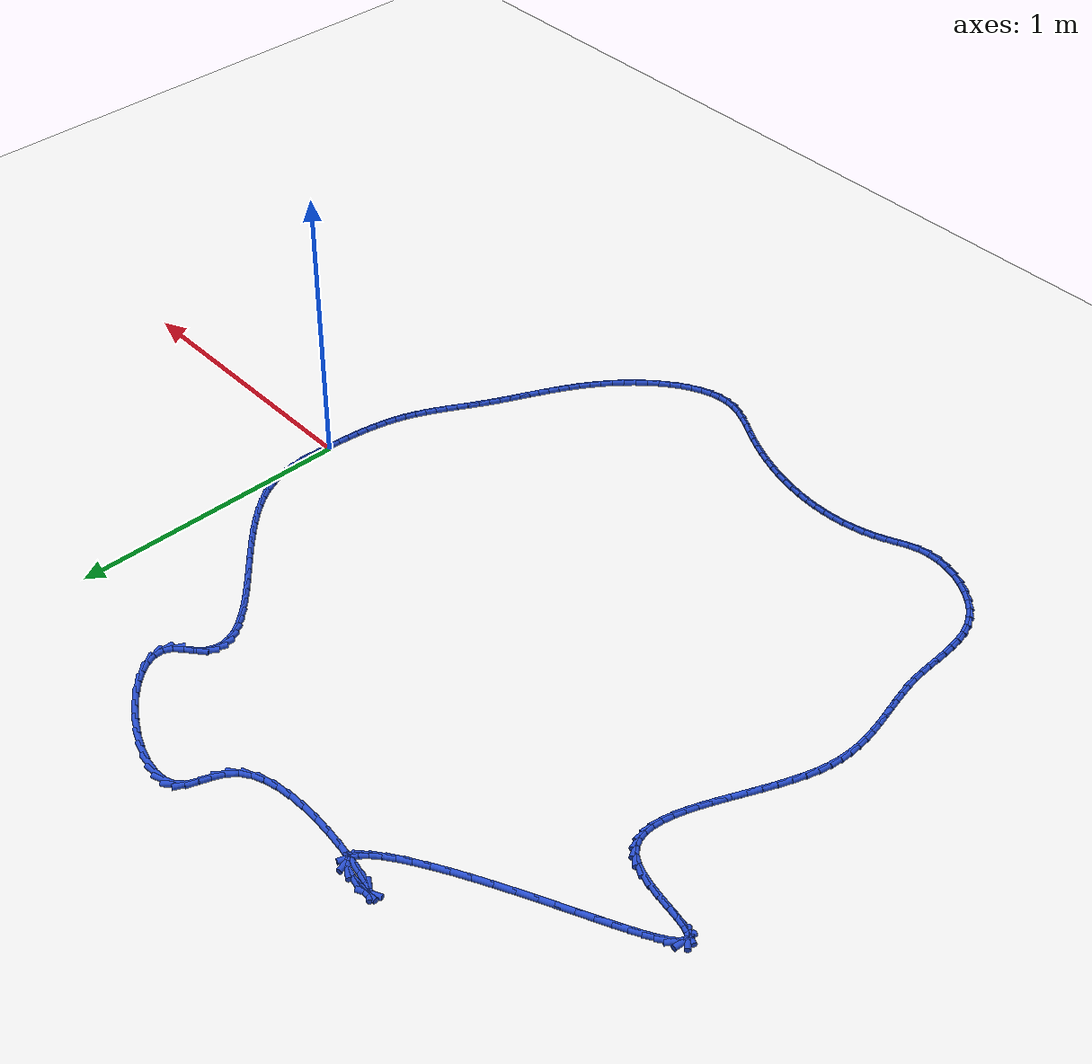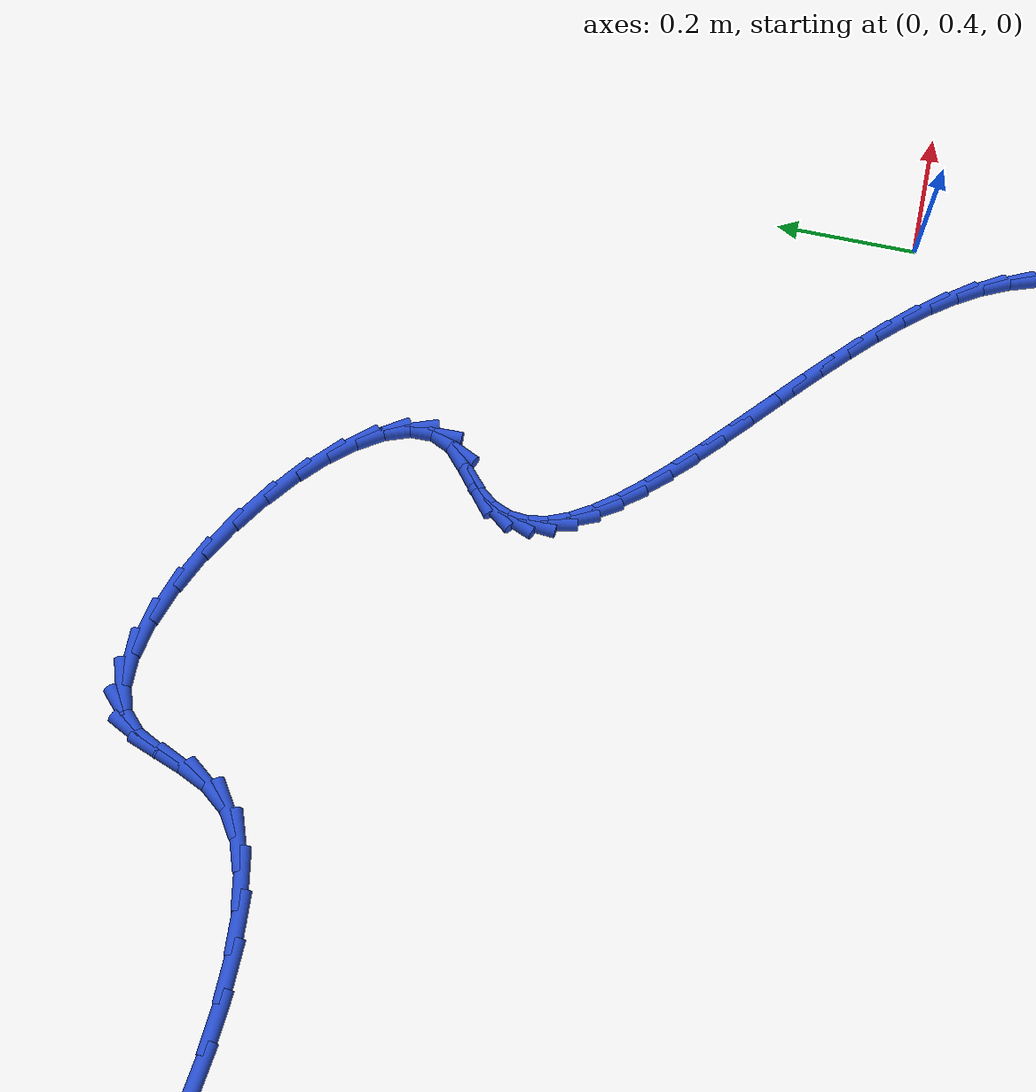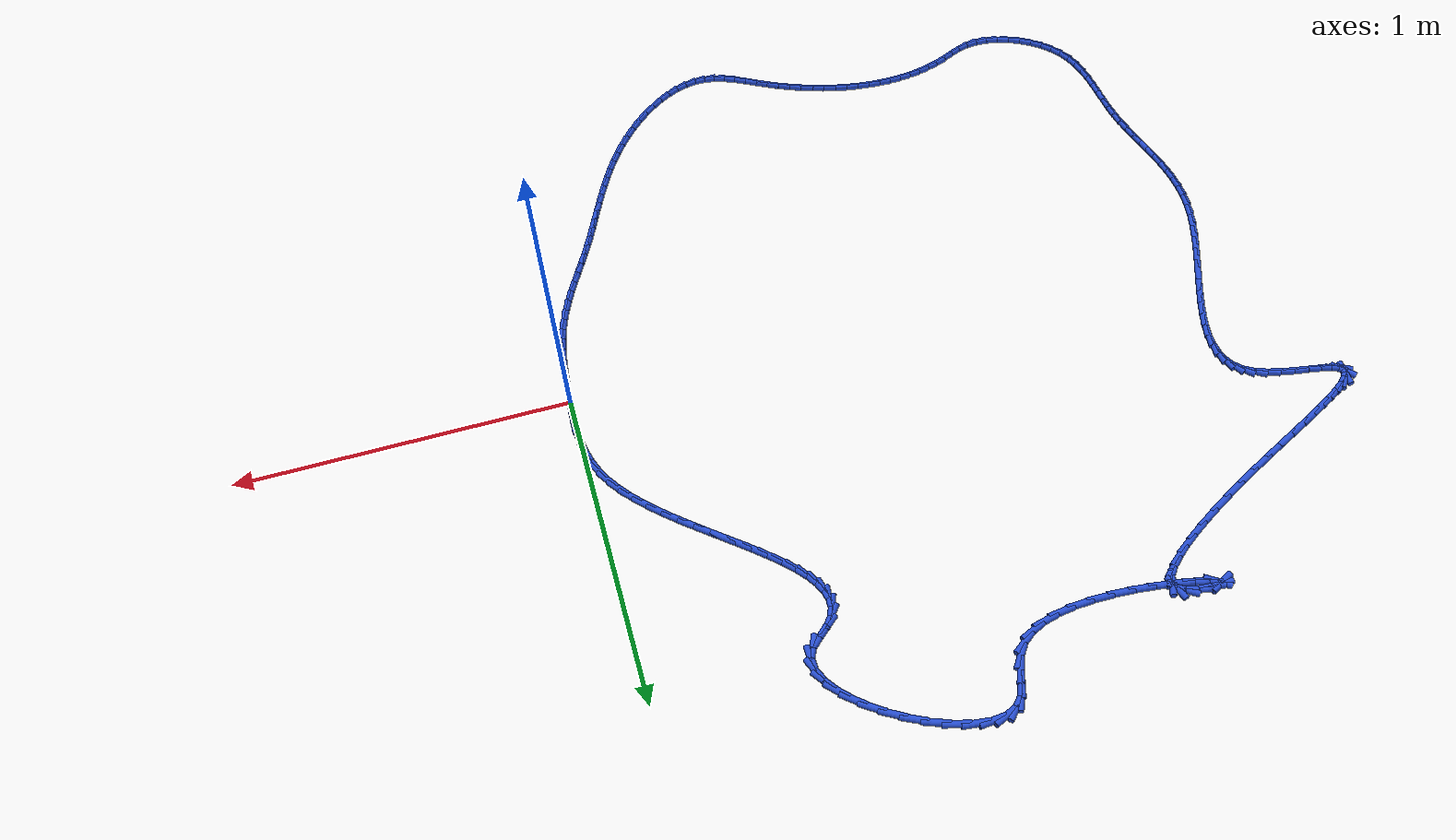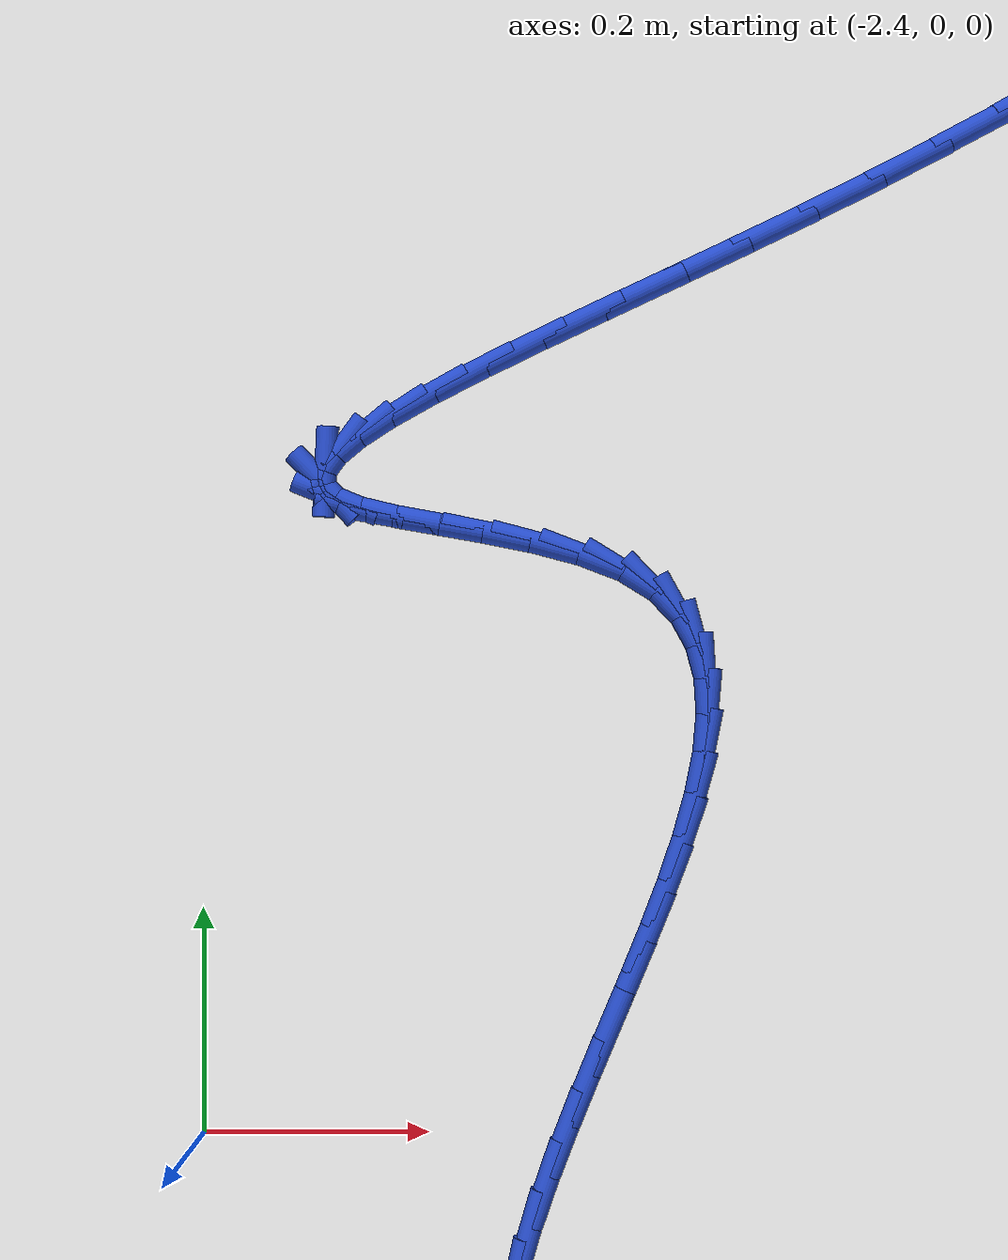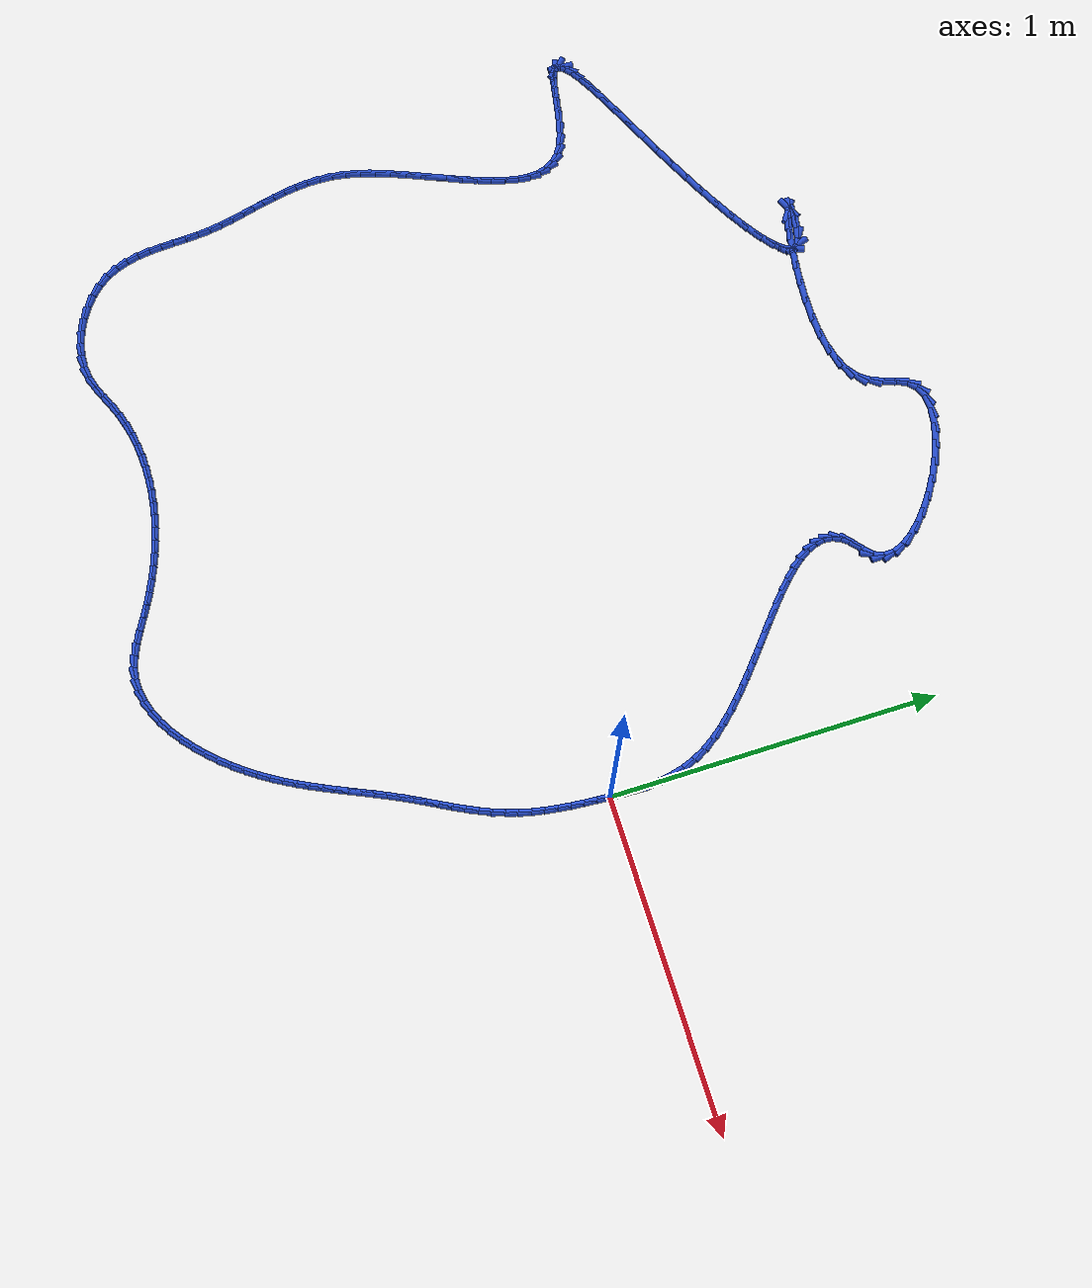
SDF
<sdf version="1.6">
 <world name="default">
  <light name="sun" type="directional">
   <pose>0 0 10 0 -0 0</pose>
   <diffuse>0.8 0.8 0.8 1</diffuse>
   <specular>0.2 0.2 0.2 1</specular>
   <attenuation>
    <range>1000</range>
    <constant>0.9</constant>
    <linear>0.01</linear>
    <quadratic>0.001</quadratic>
   </attenuation>
   <direction>-0.5 0.1 -0.9</direction>
  </light>
  <model name="ground_plane">
   <static>1</static>
   <link name="link">
    <collision name="collision">
     <geometry><plane><normal>0 0 1</normal><size>100 100</size></plane></geometry>
     <surface><friction><ode><mu>100</mu><mu2>50</mu2></ode></friction></surface>
    </collision>
    <visual name="visual">
     <cast_shadows>0</cast_shadows>
     <geometry><plane><normal>0 0 1</normal><size>100 100</size></plane></geometry>
     <material>
      <script><uri>file://media/materials/scripts/gazebo.material</uri><name>Gazebo/WhiteGlow</name></script>
     </material>
    </visual>
   </link>
  </model>
  <gravity>0 0 -9.8</gravity>
  <magnetic_field>6e-06 2.3e-05 -4.2e-05</magnetic_field>
  <atmosphere type="adiabatic"/>
  <physics name="default_physics" default="0" type="ode">
   <max_step_size>0.001</max_step_size>
   <real_time_factor>1</real_time_factor>
   <real_time_update_rate>1000</real_time_update_rate>
  </physics>
  <scene><ambient>0.4 0.4 0.4 1</ambient><background>0.7 0.7 0.7 1</background><shadows>1</shadows></scene>
  <spherical_coordinates>
   <surface_model>EARTH_WGS84</surface_model>
   <latitude_deg>0</latitude_deg>
   <longitude_deg>0</longitude_deg>
   <elevation>0</elevation>
   <heading_deg>0</heading_deg>
  </spherical_coordinates>
  <model name="line">
   <link name="link_0">
    <pose>-1.5612511283791264e-17 6.938893903907228e-18 0.01 0 1.57 1.524741888929496</pose>
    <collision name="collision">
     <geometry><cylinder><radius>0.01</radius><length>0.08</length></cylinder></geometry>
    </collision>
    <visual name="visual">
     <material>
      <script><name>Gazebo/Blue</name><uri>file://media/materials/scripts/gazebo.material</uri></script>
     </material>
     <geometry><cylinder><radius>0.01</radius><length>0.08</length></cylinder></geometry>
    </visual>
   </link>
   <link name="link_1">
    <pose>0.0017695602424048658 0.03839606043845848 0.01 0 1.57 1.5489203057388585</pose>
    <collision name="collision">
     <geometry><cylinder><radius>0.01</radius><length>0.08</length></cylinder></geometry>
    </collision>
    <visual name="visual">
     <material>
      <script><name>Gazebo/Blue</name><uri>file://media/materials/scripts/gazebo.material</uri></script>
     </material>
     <geometry><cylinder><radius>0.01</radius><length>0.08</length></cylinder></geometry>
    </visual>
   </link>
   <link name="link_2">
    <pose>0.0026070915461237354 0.07667531123249223 0.01 0 1.57 -1.5512971736761452</pose>
    <collision name="collision">
     <geometry><cylinder><radius>0.01</radius><length>0.08</length></cylinder></geometry>
    </collision>
    <visual name="visual">
     <material>
      <script><name>Gazebo/Blue</name><uri>file://media/materials/scripts/gazebo.material</uri></script>
     </material>
     <geometry><cylinder><radius>0.01</radius><length>0.08</length></cylinder></geometry>
    </visual>
   </link>
   <link name="link_3">
    <pose>0.001863651592550372 0.11479726062324151 0.01 0 1.57 -1.4925537547146386</pose>
    <collision name="collision">
     <geometry><cylinder><radius>0.01</radius><length>0.08</length></cylinder></geometry>
    </collision>
    <visual name="visual">
     <material>
      <script><name>Gazebo/Blue</name><uri>file://media/materials/scripts/gazebo.material</uri></script>
     </material>
     <geometry><cylinder><radius>0.01</radius><length>0.08</length></cylinder></geometry>
    </visual>
   </link>
   <link name="link_4">
    <pose>-0.001109701936921447 0.1527214168518466 0.01 0 1.57 -1.4167376080699157</pose>
    <collision name="collision">
     <geometry><cylinder><radius>0.01</radius><length>0.08</length></cylinder></geometry>
    </collision>
    <visual name="visual">
     <material>
      <script><name>Gazebo/Blue</name><uri>file://media/materials/scripts/gazebo.material</uri></script>
     </material>
     <geometry><cylinder><radius>0.01</radius><length>0.08</length></cylinder></geometry>
    </visual>
   </link>
   <link name="link_5">
    <pose>-0.006961911360897937 0.19040728815944785 0.01 0 1.57 -1.3251074124394193</pose>
    <collision name="collision">
     <geometry><cylinder><radius>0.01</radius><length>0.08</length></cylinder></geometry>
    </collision>
    <visual name="visual">
     <material>
      <script><name>Gazebo/Blue</name><uri>file://media/materials/scripts/gazebo.material</uri></script>
     </material>
     <geometry><cylinder><radius>0.01</radius><length>0.08</length></cylinder></geometry>
    </visual>
   </link>
   <link name="link_6">
    <pose>-0.016341918997985316 0.2278143827871855 0.01 0 1.57 -1.2203530256097037</pose>
    <collision name="collision">
     <geometry><cylinder><radius>0.01</radius><length>0.08</length></cylinder></geometry>
    </collision>
    <visual name="visual">
     <material>
      <script><name>Gazebo/Blue</name><uri>file://media/materials/scripts/gazebo.material</uri></script>
     </material>
     <geometry><cylinder><radius>0.01</radius><length>0.08</length></cylinder></geometry>
    </visual>
   </link>
   <link name="link_7">
    <pose>-0.029898667166789822 0.26490220897619987 0.01 0 1.57 -1.1067819046408895</pose>
    <collision name="collision">
     <geometry><cylinder><radius>0.01</radius><length>0.08</length></cylinder></geometry>
    </collision>
    <visual name="visual">
     <material>
      <script><name>Gazebo/Blue</name><uri>file://media/materials/scripts/gazebo.material</uri></script>
     </material>
     <geometry><cylinder><radius>0.01</radius><length>0.08</length></cylinder></geometry>
    </visual>
   </link>
   <link name="link_8">
    <pose>-0.048279553905475815 0.3016302954106456 0.01 0 1.57 -0.997281423581346</pose>
    <collision name="collision">
     <geometry><cylinder><radius>0.01</radius><length>0.08</length></cylinder></geometry>
    </collision>
    <visual name="visual">
     <material>
      <script><name>Gazebo/Blue</name><uri>file://media/materials/scripts/gazebo.material</uri></script>
     </material>
     <geometry><cylinder><radius>0.01</radius><length>0.08</length></cylinder></geometry>
    </visual>
   </link>
   <link name="link_9">
    <pose>-0.071748415662538 0.33796324832078123 0.01 0 1.57 -0.9097134440611083</pose>
    <collision name="collision">
     <geometry><cylinder><radius>0.01</radius><length>0.08</length></cylinder></geometry>
    </collision>
    <visual name="visual">
     <material>
      <script><name>Gazebo/Blue</name><uri>file://media/materials/scripts/gazebo.material</uri></script>
     </material>
     <geometry><cylinder><radius>0.01</radius><length>0.08</length></cylinder></geometry>
    </visual>
   </link>
   <link name="link_10">
    <pose>-0.09968392739692357 0.37387739160722894 0.01 0 1.57 -0.8421960164812233</pose>
    <collision name="collision">
     <geometry><cylinder><radius>0.01</radius><length>0.08</length></cylinder></geometry>
    </collision>
    <visual name="visual">
     <material>
      <script><name>Gazebo/Blue</name><uri>file://media/materials/scripts/gazebo.material</uri></script>
     </material>
     <geometry><cylinder><radius>0.01</radius><length>0.08</length></cylinder></geometry>
    </visual>
   </link>
   <link name="link_11">
    <pose>-0.1313403053092484 0.4093506967419543 0.01 0 1.57 -0.7908399223104757</pose>
    <collision name="collision">
     <geometry><cylinder><radius>0.01</radius><length>0.08</length></cylinder></geometry>
    </collision>
    <visual name="visual">
     <material>
      <script><name>Gazebo/Blue</name><uri>file://media/materials/scripts/gazebo.material</uri></script>
     </material>
     <geometry><cylinder><radius>0.01</radius><length>0.08</length></cylinder></geometry>
    </visual>
   </link>
   <link name="link_12">
    <pose>-0.16597176560012838 0.44436113519692266 0.01 0 1.57 -0.7526974474765623</pose>
    <collision name="collision">
     <geometry><cylinder><radius>0.01</radius><length>0.08</length></cylinder></geometry>
    </collision>
    <visual name="visual">
     <material>
      <script><name>Gazebo/Blue</name><uri>file://media/materials/scripts/gazebo.material</uri></script>
     </material>
     <geometry><cylinder><radius>0.01</radius><length>0.08</length></cylinder></geometry>
    </visual>
   </link>
   <link name="link_13">
    <pose>-0.20283252447017946 0.4788866784440995 0.01 0 1.57 -0.7256919706972766</pose>
    <collision name="collision">
     <geometry><cylinder><radius>0.01</radius><length>0.08</length></cylinder></geometry>
    </collision>
    <visual name="visual">
     <material>
      <script><name>Gazebo/Blue</name><uri>file://media/materials/scripts/gazebo.material</uri></script>
     </material>
     <geometry><cylinder><radius>0.01</radius><length>0.08</length></cylinder></geometry>
    </visual>
   </link>
   <link name="link_14">
    <pose>-0.24117679812001783 0.5129052979554504 0.01 0 1.57 -0.7084906442747316</pose>
    <collision name="collision">
     <geometry><cylinder><radius>0.01</radius><length>0.08</length></cylinder></geometry>
    </collision>
    <visual name="visual">
     <material>
      <script><name>Gazebo/Blue</name><uri>file://media/materials/scripts/gazebo.material</uri></script>
     </material>
     <geometry><cylinder><radius>0.01</radius><length>0.08</length></cylinder></geometry>
    </visual>
   </link>
   <link name="link_15">
    <pose>-0.280258802750259 0.5463949652029404 0.01 0 1.57 -0.7004063416435891</pose>
    <collision name="collision">
     <geometry><cylinder><radius>0.01</radius><length>0.08</length></cylinder></geometry>
    </collision>
    <visual name="visual">
     <material>
      <script><name>Gazebo/Blue</name><uri>file://media/materials/scripts/gazebo.material</uri></script>
     </material>
     <geometry><cylinder><radius>0.01</radius><length>0.08</length></cylinder></geometry>
    </visual>
   </link>
   <link name="link_16">
    <pose>-0.3193327545615192 0.5793336516585352 0.01 0 1.57 -0.7013584550680976</pose>
    <collision name="collision">
     <geometry><cylinder><radius>0.01</radius><length>0.08</length></cylinder></geometry>
    </collision>
    <visual name="visual">
     <material>
      <script><name>Gazebo/Blue</name><uri>file://media/materials/scripts/gazebo.material</uri></script>
     </material>
     <geometry><cylinder><radius>0.01</radius><length>0.08</length></cylinder></geometry>
    </visual>
   </link>
   <link name="link_17">
    <pose>-0.3576528697544143 0.6116993287942004 0.01 0 1.57 -0.7119081820319877</pose>
    <collision name="collision">
     <geometry><cylinder><radius>0.01</radius><length>0.08</length></cylinder></geometry>
    </collision>
    <visual name="visual">
     <material>
      <script><name>Gazebo/Blue</name><uri>file://media/materials/scripts/gazebo.material</uri></script>
     </material>
     <geometry><cylinder><radius>0.01</radius><length>0.08</length></cylinder></geometry>
    </visual>
   </link>
   <link name="link_18">
    <pose>-0.3944733645295602 0.643469968081901 0.01 0 1.57 -0.7333899221836887</pose>
    <collision name="collision">
     <geometry><cylinder><radius>0.01</radius><length>0.08</length></cylinder></geometry>
    </collision>
    <visual name="visual">
     <material>
      <script><name>Gazebo/Blue</name><uri>file://media/materials/scripts/gazebo.material</uri></script>
     </material>
     <geometry><cylinder><radius>0.01</radius><length>0.08</length></cylinder></geometry>
    </visual>
   </link>
   <link name="link_19">
    <pose>-0.42904845508757306 0.6746235409936031 0.01 0 1.57 -0.7681784095103517</pose>
    <collision name="collision">
     <geometry><cylinder><radius>0.01</radius><length>0.08</length></cylinder></geometry>
    </collision>
    <visual name="visual">
     <material>
      <script><name>Gazebo/Blue</name><uri>file://media/materials/scripts/gazebo.material</uri></script>
     </material>
     <geometry><cylinder><radius>0.01</radius><length>0.08</length></cylinder></geometry>
    </visual>
   </link>
   <link name="link_20">
    <pose>-0.46063235762906846 0.7051380190012713 0.01 0 1.57 -0.8201573629295184</pose>
    <collision name="collision">
     <geometry><cylinder><radius>0.01</radius><length>0.08</length></cylinder></geometry>
    </collision>
    <visual name="visual">
     <material>
      <script><name>Gazebo/Blue</name><uri>file://media/materials/scripts/gazebo.material</uri></script>
     </material>
     <geometry><cylinder><radius>0.01</radius><length>0.08</length></cylinder></geometry>
    </visual>
   </link>
   <link name="link_21">
    <pose>-0.4884792883546626 0.7349913735768715 0.01 0 1.57 -0.8954700918053922</pose>
    <collision name="collision">
     <geometry><cylinder><radius>0.01</radius><length>0.08</length></cylinder></geometry>
    </collision>
    <visual name="visual">
     <material>
      <script><name>Gazebo/Blue</name><uri>file://media/materials/scripts/gazebo.material</uri></script>
     </material>
     <geometry><cylinder><radius>0.01</radius><length>0.08</length></cylinder></geometry>
    </visual>
   </link>
   <link name="link_22">
    <pose>-0.5118434634649714 0.7641615761923694 0.01 0 1.57 -1.0035289208157723</pose>
    <collision name="collision">
     <geometry><cylinder><radius>0.01</radius><length>0.08</length></cylinder></geometry>
    </collision>
    <visual name="visual">
     <material>
      <script><name>Gazebo/Blue</name><uri>file://media/materials/scripts/gazebo.material</uri></script>
     </material>
     <geometry><cylinder><radius>0.01</radius><length>0.08</length></cylinder></geometry>
    </visual>
   </link>
   <link name="link_23">
    <pose>-0.5299790991606106 0.7926265983197295 0.01 0 1.57 -1.1575988159489503</pose>
    <collision name="collision">
     <geometry><cylinder><radius>0.01</radius><length>0.08</length></cylinder></geometry>
    </collision>
    <visual name="visual">
     <material>
      <script><name>Gazebo/Blue</name><uri>file://media/materials/scripts/gazebo.material</uri></script>
     </material>
     <geometry><cylinder><radius>0.01</radius><length>0.08</length></cylinder></geometry>
    </visual>
   </link>
   <link name="link_24">
    <pose>-0.5421404116421964 0.8203644114309181 0.01 0 1.57 -1.371851790773864</pose>
    <collision name="collision">
     <geometry><cylinder><radius>0.01</radius><length>0.08</length></cylinder></geometry>
    </collision>
    <visual name="visual">
     <material>
      <script><name>Gazebo/Blue</name><uri>file://media/materials/scripts/gazebo.material</uri></script>
     </material>
     <geometry><cylinder><radius>0.01</radius><length>0.08</length></cylinder></geometry>
    </visual>
   </link>
   <link name="link_25">
    <pose>-0.5475816171103445 0.8473529869979004 0.01 0 1.57 1.4937222623565098</pose>
    <collision name="collision">
     <geometry><cylinder><radius>0.01</radius><length>0.08</length></cylinder></geometry>
    </collision>
    <visual name="visual">
     <material>
      <script><name>Gazebo/Blue</name><uri>file://media/materials/scripts/gazebo.material</uri></script>
     </material>
     <geometry><cylinder><radius>0.01</radius><length>0.08</length></cylinder></geometry>
    </visual>
   </link>
   <link name="link_26">
    <pose>-0.5455569317656712 0.8735702964926421 0.01 0 1.57 1.188028528805704</pose>
    <collision name="collision">
     <geometry><cylinder><radius>0.01</radius><length>0.08</length></cylinder></geometry>
    </collision>
    <visual name="visual">
     <material>
      <script><name>Gazebo/Blue</name><uri>file://media/materials/scripts/gazebo.material</uri></script>
     </material>
     <geometry><cylinder><radius>0.01</radius><length>0.08</length></cylinder></geometry>
    </visual>
   </link>
   <link name="link_27">
    <pose>-0.5353205718087921 0.8989943113871081 0.01 0 1.57 0.9083943182646078</pose>
    <collision name="collision">
     <geometry><cylinder><radius>0.01</radius><length>0.08</length></cylinder></geometry>
    </collision>
    <visual name="visual">
     <material>
      <script><name>Gazebo/Blue</name><uri>file://media/materials/scripts/gazebo.material</uri></script>
     </material>
     <geometry><cylinder><radius>0.01</radius><length>0.08</length></cylinder></geometry>
    </visual>
   </link>
   <link name="link_28">
    <pose>-0.5161267534403231 0.923603003153264 0.01 0 1.57 0.6995589979222087</pose>
    <collision name="collision">
     <geometry><cylinder><radius>0.01</radius><length>0.08</length></cylinder></geometry>
    </collision>
    <visual name="visual">
     <material>
      <script><name>Gazebo/Blue</name><uri>file://media/materials/scripts/gazebo.material</uri></script>
     </material>
     <geometry><cylinder><radius>0.01</radius><length>0.08</length></cylinder></geometry>
    </visual>
   </link>
   <link name="link_29">
    <pose>-0.4877557013883198 0.9474782304685976 0.01 0 1.57 0.7387398171998228</pose>
    <collision name="collision">
     <geometry><cylinder><radius>0.01</radius><length>0.08</length></cylinder></geometry>
    </collision>
    <visual name="visual">
     <material>
      <script><name>Gazebo/Blue</name><uri>file://media/materials/scripts/gazebo.material</uri></script>
     </material>
     <geometry><cylinder><radius>0.01</radius><length>0.08</length></cylinder></geometry>
    </visual>
   </link>
   <link name="link_30">
    <pose>-0.46007120582056277 0.972692752711297 0.01 0 1.57 1.136447964704241</pose>
    <collision name="collision">
     <geometry><cylinder><radius>0.01</radius><length>0.08</length></cylinder></geometry>
    </collision>
    <visual name="visual">
     <material>
      <script><name>Gazebo/Blue</name><uri>file://media/materials/scripts/gazebo.material</uri></script>
     </material>
     <geometry><cylinder><radius>0.01</radius><length>0.08</length></cylinder></geometry>
    </visual>
   </link>
   <link name="link_31">
    <pose>-0.4465619616064606 1.00181412196866 0.01 0 1.57 -1.542672664037682</pose>
    <collision name="collision">
     <geometry><cylinder><radius>0.01</radius><length>0.08</length></cylinder></geometry>
    </collision>
    <visual name="visual">
     <material>
      <script><name>Gazebo/Blue</name><uri>file://media/materials/scripts/gazebo.material</uri></script>
     </material>
     <geometry><cylinder><radius>0.01</radius><length>0.08</length></cylinder></geometry>
    </visual>
   </link>
   <link name="link_32">
    <pose>-0.44747431749824396 1.0342464316311515 0.01 0 1.57 -1.1989750651733546</pose>
    <collision name="collision">
     <geometry><cylinder><radius>0.01</radius><length>0.08</length></cylinder></geometry>
    </collision>
    <visual name="visual">
     <material>
      <script><name>Gazebo/Blue</name><uri>file://media/materials/scripts/gazebo.material</uri></script>
     </material>
     <geometry><cylinder><radius>0.01</radius><length>0.08</length></cylinder></geometry>
    </visual>
   </link>
   <link name="link_33">
    <pose>-0.4609887171425135 1.0689023023341906 0.01 0 1.57 -0.9744169431775022</pose>
    <collision name="collision">
     <geometry><cylinder><radius>0.01</radius><length>0.08</length></cylinder></geometry>
    </collision>
    <visual name="visual">
     <material>
      <script><name>Gazebo/Blue</name><uri>file://media/materials/scripts/gazebo.material</uri></script>
     </material>
     <geometry><cylinder><radius>0.01</radius><length>0.08</length></cylinder></geometry>
    </visual>
   </link>
   <link name="link_34">
    <pose>-0.4852856041858698 1.1046943547131964 0.01 0 1.57 -0.8227326376124307</pose>
    <collision name="collision">
     <geometry><cylinder><radius>0.01</radius><length>0.08</length></cylinder></geometry>
    </collision>
    <visual name="visual">
     <material>
      <script><name>Gazebo/Blue</name><uri>file://media/materials/scripts/gazebo.material</uri></script>
     </material>
     <geometry><cylinder><radius>0.01</radius><length>0.08</length></cylinder></geometry>
    </visual>
   </link>
   <link name="link_35">
    <pose>-0.5185454222749135 1.1405352094035883 0.01 0 1.57 -0.711060561665479</pose>
    <collision name="collision">
     <geometry><cylinder><radius>0.01</radius><length>0.08</length></cylinder></geometry>
    </collision>
    <visual name="visual">
     <material>
      <script><name>Gazebo/Blue</name><uri>file://media/materials/scripts/gazebo.material</uri></script>
     </material>
     <geometry><cylinder><radius>0.01</radius><length>0.08</length></cylinder></geometry>
    </visual>
   </link>
   <link name="link_36">
    <pose>-0.5589486150562449 1.1753374870407862 0.01 0 1.57 -0.6204546544382566</pose>
    <collision name="collision">
     <geometry><cylinder><radius>0.01</radius><length>0.08</length></cylinder></geometry>
    </collision>
    <visual name="visual">
     <material>
      <script><name>Gazebo/Blue</name><uri>file://media/materials/scripts/gazebo.material</uri></script>
     </material>
     <geometry><cylinder><radius>0.01</radius><length>0.08</length></cylinder></geometry>
    </visual>
   </link>
   <link name="link_37">
    <pose>-0.6046756261764653 1.2080138082602099 0.01 0 1.57 -0.5392869423029371</pose>
    <collision name="collision">
     <geometry><cylinder><radius>0.01</radius><length>0.08</length></cylinder></geometry>
    </collision>
    <visual name="visual">
     <material>
      <script><name>Gazebo/Blue</name><uri>file://media/materials/scripts/gazebo.material</uri></script>
     </material>
     <geometry><cylinder><radius>0.01</radius><length>0.08</length></cylinder></geometry>
    </visual>
   </link>
   <link name="link_38">
    <pose>-0.6539068992821746 1.2374767936972777 0.01 0 1.57 -0.45899043763180025</pose>
    <collision name="collision">
     <geometry><cylinder><radius>0.01</radius><length>0.08</length></cylinder></geometry>
    </collision>
    <visual name="visual">
     <material>
      <script><name>Gazebo/Blue</name><uri>file://media/materials/scripts/gazebo.material</uri></script>
     </material>
     <geometry><cylinder><radius>0.01</radius><length>0.08</length></cylinder></geometry>
    </visual>
   </link>
   <link name="link_39">
    <pose>-0.7048228780199733 1.2626390639874097 0.01 0 1.57 -0.371335257415872</pose>
    <collision name="collision">
     <geometry><cylinder><radius>0.01</radius><length>0.08</length></cylinder></geometry>
    </collision>
    <visual name="visual">
     <material>
      <script><name>Gazebo/Blue</name><uri>file://media/materials/scripts/gazebo.material</uri></script>
     </material>
     <geometry><cylinder><radius>0.01</radius><length>0.08</length></cylinder></geometry>
    </visual>
   </link>
   <link name="link_40">
    <pose>-0.7556040060364625 1.2824132397660248 0.01 0 1.57 -0.2659150556534276</pose>
    <collision name="collision">
     <geometry><cylinder><radius>0.01</radius><length>0.08</length></cylinder></geometry>
    </collision>
    <visual name="visual">
     <material>
      <script><name>Gazebo/Blue</name><uri>file://media/materials/scripts/gazebo.material</uri></script>
     </material>
     <geometry><cylinder><radius>0.01</radius><length>0.08</length></cylinder></geometry>
    </visual>
   </link>
   <link name="link_41">
    <pose>-0.8044307269782427 1.2957119416685434 0.01 0 1.57 -0.12663278322390786</pose>
    <collision name="collision">
     <geometry><cylinder><radius>0.01</radius><length>0.08</length></cylinder></geometry>
    </collision>
    <visual name="visual">
     <material>
      <script><name>Gazebo/Blue</name><uri>file://media/materials/scripts/gazebo.material</uri></script>
     </material>
     <geometry><cylinder><radius>0.01</radius><length>0.08</length></cylinder></geometry>
    </visual>
   </link>
   <link name="link_42">
    <pose>-0.849483484491914 1.3014477903303843 0.01 0 1.57 0.07372422909392097</pose>
    <collision name="collision">
     <geometry><cylinder><radius>0.01</radius><length>0.08</length></cylinder></geometry>
    </collision>
    <visual name="visual">
     <material>
      <script><name>Gazebo/Blue</name><uri>file://media/materials/scripts/gazebo.material</uri></script>
     </material>
     <geometry><cylinder><radius>0.01</radius><length>0.08</length></cylinder></geometry>
    </visual>
   </link>
   <link name="link_43">
    <pose>-0.8889427222240773 1.2985334063869667 0.01 0 1.57 0.37602022117149386</pose>
    <collision name="collision">
     <geometry><cylinder><radius>0.01</radius><length>0.08</length></cylinder></geometry>
    </collision>
    <visual name="visual">
     <material>
      <script><name>Gazebo/Blue</name><uri>file://media/materials/scripts/gazebo.material</uri></script>
     </material>
     <geometry><cylinder><radius>0.01</radius><length>0.08</length></cylinder></geometry>
    </visual>
   </link>
   <link name="link_44">
    <pose>-0.9209888838213334 1.2858814104737102 0.01 0 1.57 0.7957376962847799</pose>
    <collision name="collision">
     <geometry><cylinder><radius>0.01</radius><length>0.08</length></cylinder></geometry>
    </collision>
    <visual name="visual">
     <material>
      <script><name>Gazebo/Blue</name><uri>file://media/materials/scripts/gazebo.material</uri></script>
     </material>
     <geometry><cylinder><radius>0.01</radius><length>0.08</length></cylinder></geometry>
    </visual>
   </link>
   <link name="link_45">
    <pose>-0.9439050333758008 1.2624864081774427 0.01 0 1.57 1.1330621892091943</pose>
    <collision name="collision">
     <geometry><cylinder><radius>0.01</radius><length>0.08</length></cylinder></geometry>
    </collision>
    <visual name="visual">
     <material>
      <script><name>Gazebo/Blue</name><uri>file://media/materials/scripts/gazebo.material</uri></script>
     </material>
     <geometry><cylinder><radius>0.01</radius><length>0.08</length></cylinder></geometry>
    </visual>
   </link>
   <link name="link_46">
    <pose>-0.9591611039556247 1.2298890405930683 0.01 0 1.57 1.2402261195169373</pose>
    <collision name="collision">
     <geometry><cylinder><radius>0.01</radius><length>0.08</length></cylinder></geometry>
    </collision>
    <visual name="visual">
     <material>
      <script><name>Gazebo/Blue</name><uri>file://media/materials/scripts/gazebo.material</uri></script>
     </material>
     <geometry><cylinder><radius>0.01</radius><length>0.08</length></cylinder></geometry>
    </visual>
   </link>
   <link name="link_47">
    <pose>-0.9719545670697183 1.1926079329432684 0.01 0 1.57 1.171265808478501</pose>
    <collision name="collision">
     <geometry><cylinder><radius>0.01</radius><length>0.08</length></cylinder></geometry>
    </collision>
    <visual name="visual">
     <material>
      <script><name>Gazebo/Blue</name><uri>file://media/materials/scripts/gazebo.material</uri></script>
     </material>
     <geometry><cylinder><radius>0.01</radius><length>0.08</length></cylinder></geometry>
    </visual>
   </link>
   <link name="link_48">
    <pose>-0.9876944816956905 1.1553307507258093 0.01 0 1.57 0.9349053990979008</pose>
    <collision name="collision">
     <geometry><cylinder><radius>0.01</radius><length>0.08</length></cylinder></geometry>
    </collision>
    <visual name="visual">
     <material>
      <script><name>Gazebo/Blue</name><uri>file://media/materials/scripts/gazebo.material</uri></script>
     </material>
     <geometry><cylinder><radius>0.01</radius><length>0.08</length></cylinder></geometry>
    </visual>
   </link>
   <link name="link_49">
    <pose>-1.0117629140037727 1.1227254900117059 0.01 0 1.57 0.6185591939464439</pose>
    <collision name="collision">
     <geometry><cylinder><radius>0.01</radius><length>0.08</length></cylinder></geometry>
    </collision>
    <visual name="visual">
     <material>
      <script><name>Gazebo/Blue</name><uri>file://media/materials/scripts/gazebo.material</uri></script>
     </material>
     <geometry><cylinder><radius>0.01</radius><length>0.08</length></cylinder></geometry>
    </visual>
   </link>
   <link name="link_50">
    <pose>-1.04702646401402 1.0976271483071323 0.01 0 1.57 0.3831009308370855</pose>
    <collision name="collision">
     <geometry><cylinder><radius>0.01</radius><length>0.08</length></cylinder></geometry>
    </collision>
    <visual name="visual">
     <material>
      <script><name>Gazebo/Blue</name><uri>file://media/materials/scripts/gazebo.material</uri></script>
     </material>
     <geometry><cylinder><radius>0.01</radius><length>0.08</length></cylinder></geometry>
    </visual>
   </link>
   <link name="link_51">
    <pose>-1.0918255580740293 1.0795725392626503 0.01 0 1.57 0.22265292155680552</pose>
    <collision name="collision">
     <geometry><cylinder><radius>0.01</radius><length>0.08</length></cylinder></geometry>
    </collision>
    <visual name="visual">
     <material>
      <script><name>Gazebo/Blue</name><uri>file://media/materials/scripts/gazebo.material</uri></script>
     </material>
     <geometry><cylinder><radius>0.01</radius><length>0.08</length></cylinder></geometry>
    </visual>
   </link>
   <link name="link_52">
    <pose>-1.1440274534296377 1.0677536822709524 0.01 0 1.57 0.11074853608529343</pose>
    <collision name="collision">
     <geometry><cylinder><radius>0.01</radius><length>0.08</length></cylinder></geometry>
    </collision>
    <visual name="visual">
     <material>
      <script><name>Gazebo/Blue</name><uri>file://media/materials/scripts/gazebo.material</uri></script>
     </material>
     <geometry><cylinder><radius>0.01</radius><length>0.08</length></cylinder></geometry>
    </visual>
   </link>
   <link name="link_53">
    <pose>-1.201499407326686 1.0613625967247309 0.01 0 1.57 0.029216499290346757</pose>
    <collision name="collision">
     <geometry><cylinder><radius>0.01</radius><length>0.08</length></cylinder></geometry>
    </collision>
    <visual name="visual">
     <material>
      <script><name>Gazebo/Blue</name><uri>file://media/materials/scripts/gazebo.material</uri></script>
     </material>
     <geometry><cylinder><radius>0.01</radius><length>0.08</length></cylinder></geometry>
    </visual>
   </link>
   <link name="link_54">
    <pose>-1.2621086770110108 1.0595913020166778 0.01 0 1.57 -0.03310570998613322</pose>
    <collision name="collision">
     <geometry><cylinder><radius>0.01</radius><length>0.08</length></cylinder></geometry>
    </collision>
    <visual name="visual">
     <material>
      <script><name>Gazebo/Blue</name><uri>file://media/materials/scripts/gazebo.material</uri></script>
     </material>
     <geometry><cylinder><radius>0.01</radius><length>0.08</length></cylinder></geometry>
    </visual>
   </link>
   <link name="link_55">
    <pose>-1.3237225197284512 1.0616318175394845 0.01 0 1.57 -0.08320481173974842</pose>
    <collision name="collision">
     <geometry><cylinder><radius>0.01</radius><length>0.08</length></cylinder></geometry>
    </collision>
    <visual name="visual">
     <material>
      <script><name>Gazebo/Blue</name><uri>file://media/materials/scripts/gazebo.material</uri></script>
     </material>
     <geometry><cylinder><radius>0.01</radius><length>0.08</length></cylinder></geometry>
    </visual>
   </link>
   <link name="link_56">
    <pose>-1.3842081927248475 1.0666761626858443 0.01 0 1.57 -0.1258533491783362</pose>
    <collision name="collision">
     <geometry><cylinder><radius>0.01</radius><length>0.08</length></cylinder></geometry>
    </collision>
    <visual name="visual">
     <material>
      <script><name>Gazebo/Blue</name><uri>file://media/materials/scripts/gazebo.material</uri></script>
     </material>
     <geometry><cylinder><radius>0.01</radius><length>0.08</length></cylinder></geometry>
    </visual>
   </link>
   <link name="link_57">
    <pose>-1.4414329532460368 1.0739163568484489 0.01 0 1.57 -0.16495241027521698</pose>
    <collision name="collision">
     <geometry><cylinder><radius>0.01</radius><length>0.08</length></cylinder></geometry>
    </collision>
    <visual name="visual">
     <material>
      <script><name>Gazebo/Blue</name><uri>file://media/materials/scripts/gazebo.material</uri></script>
     </material>
     <geometry><cylinder><radius>0.01</radius><length>0.08</length></cylinder></geometry>
    </visual>
   </link>
   <link name="link_58">
    <pose>-1.4932640585378585 1.0825444194199902 0.01 0 1.57 -0.20491517443810128</pose>
    <collision name="collision">
     <geometry><cylinder><radius>0.01</radius><length>0.08</length></cylinder></geometry>
    </collision>
    <visual name="visual">
     <material>
      <script><name>Gazebo/Blue</name><uri>file://media/materials/scripts/gazebo.material</uri></script>
     </material>
     <geometry><cylinder><radius>0.01</radius><length>0.08</length></cylinder></geometry>
    </visual>
   </link>
   <link name="link_59">
    <pose>-1.5375687658461508 1.0917523697931601 0.01 0 1.57 -0.2536111768307435</pose>
    <collision name="collision">
     <geometry><cylinder><radius>0.01</radius><length>0.08</length></cylinder></geometry>
    </collision>
    <visual name="visual">
     <material>
      <script><name>Gazebo/Blue</name><uri>file://media/materials/scripts/gazebo.material</uri></script>
     </material>
     <geometry><cylinder><radius>0.01</radius><length>0.08</length></cylinder></geometry>
    </visual>
   </link>
   <link name="link_60">
    <pose>-1.5722143324167532 1.1007322273606517 0.01 0 1.57 -0.33452904336762457</pose>
    <collision name="collision">
     <geometry><cylinder><radius>0.01</radius><length>0.08</length></cylinder></geometry>
    </collision>
    <visual name="visual">
     <material>
      <script><name>Gazebo/Blue</name><uri>file://media/materials/scripts/gazebo.material</uri></script>
     </material>
     <geometry><cylinder><radius>0.01</radius><length>0.08</length></cylinder></geometry>
    </visual>
   </link>
   <link name="link_61">
    <pose>-1.5950680154955037 1.1086760115151562 0.01 0 1.57 -0.5993156591058151</pose>
    <collision name="collision">
     <geometry><cylinder><radius>0.01</radius><length>0.08</length></cylinder></geometry>
    </collision>
    <visual name="visual">
     <material>
      <script><name>Gazebo/Blue</name><uri>file://media/materials/scripts/gazebo.material</uri></script>
     </material>
     <geometry><cylinder><radius>0.01</radius><length>0.08</length></cylinder></geometry>
    </visual>
   </link>
   <link name="link_62">
    <pose>-1.6039970723282413 1.114775741649366 0.01 0 1.57 0.45049219160449977</pose>
    <collision name="collision">
     <geometry><cylinder><radius>0.01</radius><length>0.08</length></cylinder></geometry>
    </collision>
    <visual name="visual">
     <material>
      <script><name>Gazebo/Blue</name><uri>file://media/materials/scripts/gazebo.material</uri></script>
     </material>
     <geometry><cylinder><radius>0.01</radius><length>0.08</length></cylinder></geometry>
    </visual>
   </link>
   <link name="link_63">
    <pose>-1.596868760160805 1.1182234371559736 0.01 0 1.57 -0.00045436109669818274</pose>
    <collision name="collision">
     <geometry><cylinder><radius>0.01</radius><length>0.08</length></cylinder></geometry>
    </collision>
    <visual name="visual">
     <material>
      <script><name>Gazebo/Blue</name><uri>file://media/materials/scripts/gazebo.material</uri></script>
     </material>
     <geometry><cylinder><radius>0.01</radius><length>0.08</length></cylinder></geometry>
    </visual>
   </link>
   <link name="link_64">
    <pose>-1.5715867153292318 1.1182119499775667 0.01 0 1.57 -0.10538714081509594</pose>
    <collision name="collision">
     <geometry><cylinder><radius>0.01</radius><length>0.08</length></cylinder></geometry>
    </collision>
    <visual name="visual">
     <material>
      <script><name>Gazebo/Blue</name><uri>file://media/materials/scripts/gazebo.material</uri></script>
     </material>
     <geometry><cylinder><radius>0.01</radius><length>0.08</length></cylinder></geometry>
    </visual>
   </link>
   <link name="link_65">
    <pose>-1.5325511916757233 1.1140828097229545 0.01 0 1.57 -0.24223994316319153</pose>
    <collision name="collision">
     <geometry><cylinder><radius>0.01</radius><length>0.08</length></cylinder></geometry>
    </collision>
    <visual name="visual">
     <material>
      <script><name>Gazebo/Blue</name><uri>file://media/materials/scripts/gazebo.material</uri></script>
     </material>
     <geometry><cylinder><radius>0.01</radius><length>0.08</length></cylinder></geometry>
    </visual>
   </link>
   <link name="link_66">
    <pose>-1.4978407646117895 1.1055061376246496 0.01 0 1.57 -0.5826988297386786</pose>
    <collision name="collision">
     <geometry><cylinder><radius>0.01</radius><length>0.08</length></cylinder></geometry>
    </collision>
    <visual name="visual">
     <material>
      <script><name>Gazebo/Blue</name><uri>file://media/materials/scripts/gazebo.material</uri></script>
     </material>
     <geometry><cylinder><radius>0.01</radius><length>0.08</length></cylinder></geometry>
    </visual>
   </link>
   <link name="link_67">
    <pose>-1.4781532363193755 1.0925314150318177 0.01 0 1.57 -1.2628715336598104</pose>
    <collision name="collision">
     <geometry><cylinder><radius>0.01</radius><length>0.08</length></cylinder></geometry>
    </collision>
    <visual name="visual">
     <material>
      <script><name>Gazebo/Blue</name><uri>file://media/materials/scripts/gazebo.material</uri></script>
     </material>
     <geometry><cylinder><radius>0.01</radius><length>0.08</length></cylinder></geometry>
    </visual>
   </link>
   <link name="link_68">
    <pose>-1.4727773109878248 1.0756281623570447 0.01 0 1.57 1.2169457573293934</pose>
    <collision name="collision">
     <geometry><cylinder><radius>0.01</radius><length>0.08</length></cylinder></geometry>
    </collision>
    <visual name="visual">
     <material>
      <script><name>Gazebo/Blue</name><uri>file://media/materials/scripts/gazebo.material</uri></script>
     </material>
     <geometry><cylinder><radius>0.01</radius><length>0.08</length></cylinder></geometry>
    </visual>
   </link>
   <link name="link_69">
    <pose>-1.480289409153508 1.0552921235547483 0.01 0 1.57 0.8867438918955234</pose>
    <collision name="collision">
     <geometry><cylinder><radius>0.01</radius><length>0.08</length></cylinder></geometry>
    </collision>
    <visual name="visual">
     <material>
      <script><name>Gazebo/Blue</name><uri>file://media/materials/scripts/gazebo.material</uri></script>
     </material>
     <geometry><cylinder><radius>0.01</radius><length>0.08</length></cylinder></geometry>
    </visual>
   </link>
   <link name="link_70">
    <pose>-1.4992659513527973 1.0320190425793483 0.01 0 1.57 0.7251219211130178</pose>
    <collision name="collision">
     <geometry><cylinder><radius>0.01</radius><length>0.08</length></cylinder></geometry>
    </collision>
    <visual name="visual">
     <material>
      <script><name>Gazebo/Blue</name><uri>file://media/materials/scripts/gazebo.material</uri></script>
     </material>
     <geometry><cylinder><radius>0.01</radius><length>0.08</length></cylinder></geometry>
    </visual>
   </link>
   <link name="link_71">
    <pose>-1.5282833581220614 1.0063046633852615 0.01 0 1.57 0.6338047884958683</pose>
    <collision name="collision">
     <geometry><cylinder><radius>0.01</radius><length>0.08</length></cylinder></geometry>
    </collision>
    <visual name="visual">
     <material>
      <script><name>Gazebo/Blue</name><uri>file://media/materials/scripts/gazebo.material</uri></script>
     </material>
     <geometry><cylinder><radius>0.01</radius><length>0.08</length></cylinder></geometry>
    </visual>
   </link>
   <link name="link_72">
    <pose>-1.5659180499976721 0.9786447299269071 0.01 0 1.57 0.5759247933292906</pose>
    <collision name="collision">
     <geometry><cylinder><radius>0.01</radius><length>0.08</length></cylinder></geometry>
    </collision>
    <visual name="visual">
     <material>
      <script><name>Gazebo/Blue</name><uri>file://media/materials/scripts/gazebo.material</uri></script>
     </material>
     <geometry><cylinder><radius>0.01</radius><length>0.08</length></cylinder></geometry>
    </visual>
   </link>
   <link name="link_73">
    <pose>-1.6107464475159996 0.9495349861587024 0.01 0 1.57 0.5361171110174496</pose>
    <collision name="collision">
     <geometry><cylinder><radius>0.01</radius><length>0.08</length></cylinder></geometry>
    </collision>
    <visual name="visual">
     <material>
      <script><name>Gazebo/Blue</name><uri>file://media/materials/scripts/gazebo.material</uri></script>
     </material>
     <geometry><cylinder><radius>0.01</radius><length>0.08</length></cylinder></geometry>
    </visual>
   </link>
   <link name="link_74">
    <pose>-1.6613449712134147 0.919471176035067 0.01 0 1.57 0.5070580799081065</pose>
    <collision name="collision">
     <geometry><cylinder><radius>0.01</radius><length>0.08</length></cylinder></geometry>
    </collision>
    <visual name="visual">
     <material>
      <script><name>Gazebo/Blue</name><uri>file://media/materials/scripts/gazebo.material</uri></script>
     </material>
     <geometry><cylinder><radius>0.01</radius><length>0.08</length></cylinder></geometry>
    </visual>
   </link>
   <link name="link_75">
    <pose>-1.716290041626288 0.8889490435104186 0.01 0 1.57 0.4848547123283656</pose>
    <collision name="collision">
     <geometry><cylinder><radius>0.01</radius><length>0.08</length></cylinder></geometry>
    </collision>
    <visual name="visual">
     <material>
      <script><name>Gazebo/Blue</name><uri>file://media/materials/scripts/gazebo.material</uri></script>
     </material>
     <geometry><cylinder><radius>0.01</radius><length>0.08</length></cylinder></geometry>
    </visual>
   </link>
   <link name="link_76">
    <pose>-1.774158079290991 0.8584643325391752 0.01 0 1.57 0.4672502462934384</pose>
    <collision name="collision">
     <geometry><cylinder><radius>0.01</radius><length>0.08</length></cylinder></geometry>
    </collision>
    <visual name="visual">
     <material>
      <script><name>Gazebo/Blue</name><uri>file://media/materials/scripts/gazebo.material</uri></script>
     </material>
     <geometry><cylinder><radius>0.01</radius><length>0.08</length></cylinder></geometry>
    </visual>
   </link>
   <link name="link_77">
    <pose>-1.8335255047438936 0.8285127870757562 0.01 0 1.57 0.4529797296420567</pose>
    <collision name="collision">
     <geometry><cylinder><radius>0.01</radius><length>0.08</length></cylinder></geometry>
    </collision>
    <visual name="visual">
     <material>
      <script><name>Gazebo/Blue</name><uri>file://media/materials/scripts/gazebo.material</uri></script>
     </material>
     <geometry><cylinder><radius>0.01</radius><length>0.08</length></cylinder></geometry>
    </visual>
   </link>
   <link name="link_78">
    <pose>-1.8930017533487251 0.7995635914094978 0.01 0 1.57 0.4426449568052987</pose>
    <collision name="collision">
     <geometry><cylinder><radius>0.01</radius><length>0.08</length></cylinder></geometry>
    </collision>
    <visual name="visual">
     <material>
      <script><name>Gazebo/Blue</name><uri>file://media/materials/scripts/gazebo.material</uri></script>
     </material>
     <geometry><cylinder><radius>0.01</radius><length>0.08</length></cylinder></geometry>
    </visual>
   </link>
   <link name="link_79">
    <pose>-1.9515214133271221 0.7718243518753135 0.01 0 1.57 0.4368961481491594</pose>
    <collision name="collision">
     <geometry><cylinder><radius>0.01</radius><length>0.08</length></cylinder></geometry>
    </collision>
    <visual name="visual">
     <material>
      <script><name>Gazebo/Blue</name><uri>file://media/materials/scripts/gazebo.material</uri></script>
     </material>
     <geometry><cylinder><radius>0.01</radius><length>0.08</length></cylinder></geometry>
    </visual>
   </link>
   <link name="link_80">
    <pose>-2.0082039907340667 0.7453539126877589 0.01 0 1.57 0.43601604499487856</pose>
    <collision name="collision">
     <geometry><cylinder><radius>0.01</radius><length>0.08</length></cylinder></geometry>
    </collision>
    <visual name="visual">
     <material>
      <script><name>Gazebo/Blue</name><uri>file://media/materials/scripts/gazebo.material</uri></script>
     </material>
     <geometry><cylinder><radius>0.01</radius><length>0.08</length></cylinder></geometry>
    </visual>
   </link>
   <link name="link_81">
    <pose>-2.062171127285192 0.720209399971786 0.01 0 1.57 0.4407581861228284</pose>
    <collision name="collision">
     <geometry><cylinder><radius>0.01</radius><length>0.08</length></cylinder></geometry>
    </collision>
    <visual name="visual">
     <material>
      <script><name>Gazebo/Blue</name><uri>file://media/materials/scripts/gazebo.material</uri></script>
     </material>
     <geometry><cylinder><radius>0.01</radius><length>0.08</length></cylinder></geometry>
    </visual>
   </link>
   <link name="link_82">
    <pose>-2.11254446469613 0.6964479398523468 0.01 0 1.57 0.45261951568819364</pose>
    <collision name="collision">
     <geometry><cylinder><radius>0.01</radius><length>0.08</length></cylinder></geometry>
    </collision>
    <visual name="visual">
     <material>
      <script><name>Gazebo/Blue</name><uri>file://media/materials/scripts/gazebo.material</uri></script>
     </material>
     <geometry><cylinder><radius>0.01</radius><length>0.08</length></cylinder></geometry>
    </visual>
   </link>
   <link name="link_83">
    <pose>-2.158445644682515 0.6741266584543946 0.01 0 1.57 0.474412810399847</pose>
    <collision name="collision">
     <geometry><cylinder><radius>0.01</radius><length>0.08</length></cylinder></geometry>
    </collision>
    <visual name="visual">
     <material>
      <script><name>Gazebo/Blue</name><uri>file://media/materials/scripts/gazebo.material</uri></script>
     </material>
     <geometry><cylinder><radius>0.01</radius><length>0.08</length></cylinder></geometry>
    </visual>
   </link>
   <link name="link_84">
    <pose>-2.1989963089599773 0.6533026819028814 0.01 0 1.57 0.5115820928979206</pose>
    <collision name="collision">
     <geometry><cylinder><radius>0.01</radius><length>0.08</length></cylinder></geometry>
    </collision>
    <visual name="visual">
     <material>
      <script><name>Gazebo/Blue</name><uri>file://media/materials/scripts/gazebo.material</uri></script>
     </material>
     <geometry><cylinder><radius>0.01</radius><length>0.08</length></cylinder></geometry>
    </visual>
   </link>
   <link name="link_85">
    <pose>-2.233318099244151 0.6340331363227594 0.01 0 1.57 0.5755617705309598</pose>
    <collision name="collision">
     <geometry><cylinder><radius>0.01</radius><length>0.08</length></cylinder></geometry>
    </collision>
    <visual name="visual">
     <material>
      <script><name>Gazebo/Blue</name><uri>file://media/materials/scripts/gazebo.material</uri></script>
     </material>
     <geometry><cylinder><radius>0.01</radius><length>0.08</length></cylinder></geometry>
    </visual>
   </link>
   <link name="link_86">
    <pose>-2.2605326572506685 0.6163751478389815 0.01 0 1.57 0.6936682105934229</pose>
    <collision name="collision">
     <geometry><cylinder><radius>0.01</radius><length>0.08</length></cylinder></geometry>
    </collision>
    <visual name="visual">
     <material>
      <script><name>Gazebo/Blue</name><uri>file://media/materials/scripts/gazebo.material</uri></script>
     </material>
     <geometry><cylinder><radius>0.01</radius><length>0.08</length></cylinder></geometry>
    </visual>
   </link>
   <link name="link_87">
    <pose>-2.2797616246951615 0.6003858425765 0.01 0 1.57 0.9423868441744991</pose>
    <collision name="collision">
     <geometry><cylinder><radius>0.01</radius><length>0.08</length></cylinder></geometry>
    </collision>
    <visual name="visual">
     <material>
      <script><name>Gazebo/Blue</name><uri>file://media/materials/scripts/gazebo.material</uri></script>
     </material>
     <geometry><cylinder><radius>0.01</radius><length>0.08</length></cylinder></geometry>
    </visual>
   </link>
   <link name="link_88">
    <pose>-2.290126643293265 0.5861223466602673 0.01 0 1.57 1.5209431570071748</pose>
    <collision name="collision">
     <geometry><cylinder><radius>0.01</radius><length>0.08</length></cylinder></geometry>
    </collision>
    <visual name="visual">
     <material>
      <script><name>Gazebo/Blue</name><uri>file://media/materials/scripts/gazebo.material</uri></script>
     </material>
     <geometry><cylinder><radius>0.01</radius><length>0.08</length></cylinder></geometry>
    </visual>
   </link>
   <link name="link_89">
    <pose>-2.2907493547606097 0.5736417862152358 0.01 0 1.57 -0.8165214953865673</pose>
    <collision name="collision">
     <geometry><cylinder><radius>0.01</radius><length>0.08</length></cylinder></geometry>
    </collision>
    <visual name="visual">
     <material>
      <script><name>Gazebo/Blue</name><uri>file://media/materials/scripts/gazebo.material</uri></script>
     </material>
     <geometry><cylinder><radius>0.01</radius><length>0.08</length></cylinder></geometry>
    </visual>
   </link>
   <link name="link_90">
    <pose>-2.2807514008128287 0.5630012873663579 0.01 0 1.57 -0.39126328102824415</pose>
    <collision name="collision">
     <geometry><cylinder><radius>0.01</radius><length>0.08</length></cylinder></geometry>
    </collision>
    <visual name="visual">
     <material>
      <script><name>Gazebo/Blue</name><uri>file://media/materials/scripts/gazebo.material</uri></script>
     </material>
     <geometry><cylinder><radius>0.01</radius><length>0.08</length></cylinder></geometry>
    </visual>
   </link>
   <link name="link_91">
    <pose>-2.2594435639553536 0.5542111139494484 0.01 0 1.57 -0.2355901098909157</pose>
    <collision name="collision">
     <geometry><cylinder><radius>0.01</radius><length>0.08</length></cylinder></geometry>
    </collision>
    <visual name="visual">
     <material>
      <script><name>Gazebo/Blue</name><uri>file://media/materials/scripts/gazebo.material</uri></script>
     </material>
     <geometry><cylinder><radius>0.01</radius><length>0.08</length></cylinder></geometry>
    </visual>
   </link>
   <link name="link_92">
    <pose>-2.2283212202978593 0.5467402660293496 0.01 0 1.57 -0.18275115758788868</pose>
    <collision name="collision">
     <geometry><cylinder><radius>0.01</radius><length>0.08</length></cylinder></geometry>
    </collision>
    <visual name="visual">
     <material>
      <script><name>Gazebo/Blue</name><uri>file://media/materials/scripts/gazebo.material</uri></script>
     </material>
     <geometry><cylinder><radius>0.01</radius><length>0.08</length></cylinder></geometry>
    </visual>
   </link>
   <link name="link_93">
    <pose>-2.1902824626655937 0.5397102008887582 0.01 0 1.57 -0.17595882089147952</pose>
    <collision name="collision">
     <geometry><cylinder><radius>0.01</radius><length>0.08</length></cylinder></geometry>
    </collision>
    <visual name="visual">
     <material>
      <script><name>Gazebo/Blue</name><uri>file://media/materials/scripts/gazebo.material</uri></script>
     </material>
     <geometry><cylinder><radius>0.01</radius><length>0.08</length></cylinder></geometry>
    </visual>
   </link>
   <link name="link_94">
    <pose>-2.1482484633819854 0.5322366575403037 0.01 0 1.57 -0.2013998961068839</pose>
    <collision name="collision">
     <geometry><cylinder><radius>0.01</radius><length>0.08</length></cylinder></geometry>
    </collision>
    <visual name="visual">
     <material>
      <script><name>Gazebo/Blue</name><uri>file://media/materials/scripts/gazebo.material</uri></script>
     </material>
     <geometry><cylinder><radius>0.01</radius><length>0.08</length></cylinder></geometry>
    </visual>
   </link>
   <link name="link_95">
    <pose>-2.10514039477046 0.5234353749966151 0.01 0 1.57 -0.2608367597978506</pose>
    <collision name="collision">
     <geometry><cylinder><radius>0.01</radius><length>0.08</length></cylinder></geometry>
    </collision>
    <visual name="visual">
     <material>
      <script><name>Gazebo/Blue</name><uri>file://media/materials/scripts/gazebo.material</uri></script>
     </material>
     <geometry><cylinder><radius>0.01</radius><length>0.08</length></cylinder></geometry>
    </visual>
   </link>
   <link name="link_96">
    <pose>-2.0638794291544493 0.5124220922703218 0.01 0 1.57 -0.368936588976419</pose>
    <collision name="collision">
     <geometry><cylinder><radius>0.01</radius><length>0.08</length></cylinder></geometry>
    </collision>
    <visual name="visual">
     <material>
      <script><name>Gazebo/Blue</name><uri>file://media/materials/scripts/gazebo.material</uri></script>
     </material>
     <geometry><cylinder><radius>0.01</radius><length>0.08</length></cylinder></geometry>
    </visual>
   </link>
   <link name="link_97">
    <pose>-2.02738673885738 0.4983125483740532 0.01 0 1.57 -0.5541475041922188</pose>
    <collision name="collision">
     <geometry><cylinder><radius>0.01</radius><length>0.08</length></cylinder></geometry>
    </collision>
    <visual name="visual">
     <material>
      <script><name>Gazebo/Blue</name><uri>file://media/materials/scripts/gazebo.material</uri></script>
     </material>
     <geometry><cylinder><radius>0.01</radius><length>0.08</length></cylinder></geometry>
    </visual>
   </link>
   <link name="link_98">
    <pose>-1.9983035779487073 0.480315122445728 0.01 0 1.57 -0.8005488677296165</pose>
    <collision name="collision">
     <geometry><cylinder><radius>0.01</radius><length>0.08</length></cylinder></geometry>
    </collision>
    <visual name="visual">
     <material>
      <script><name>Gazebo/Blue</name><uri>file://media/materials/scripts/gazebo.material</uri></script>
     </material>
     <geometry><cylinder><radius>0.01</radius><length>0.08</length></cylinder></geometry>
    </visual>
   </link>
   <link name="link_99">
    <pose>-1.9770248380075843 0.45838163675209276 0.01 0 1.57 -1.0648889801595527</pose>
    <collision name="collision">
     <geometry><cylinder><radius>0.01</radius><length>0.08</length></cylinder></geometry>
    </collision>
    <visual name="visual">
     <material>
      <script><name>Gazebo/Blue</name><uri>file://media/materials/scripts/gazebo.material</uri></script>
     </material>
     <geometry><cylinder><radius>0.01</radius><length>0.08</length></cylinder></geometry>
    </visual>
   </link>
   <link name="link_100">
    <pose>-1.9628646347166427 0.43282160089554766 0.01 0 1.57 -1.3090786006979642</pose>
    <collision name="collision">
     <geometry><cylinder><radius>0.01</radius><length>0.08</length></cylinder></geometry>
    </collision>
    <visual name="visual">
     <material>
      <script><name>Gazebo/Blue</name><uri>file://media/materials/scripts/gazebo.material</uri></script>
     </material>
     <geometry><cylinder><radius>0.01</radius><length>0.08</length></cylinder></geometry>
    </visual>
   </link>
   <link name="link_101">
    <pose>-1.9551301844388116 0.4039468078374122 0.01 0 1.57 -1.5080925087312016</pose>
    <collision name="collision">
     <geometry><cylinder><radius>0.01</radius><length>0.08</length></cylinder></geometry>
    </collision>
    <visual name="visual">
     <material>
      <script><name>Gazebo/Blue</name><uri>file://media/materials/scripts/gazebo.material</uri></script>
     </material>
     <geometry><cylinder><radius>0.01</radius><length>0.08</length></cylinder></geometry>
    </visual>
   </link>
   <link name="link_102">
    <pose>-1.953128703537015 0.3720690505390066 0.01 0 1.57 1.4831189106805307</pose>
    <collision name="collision">
     <geometry><cylinder><radius>0.01</radius><length>0.08</length></cylinder></geometry>
    </collision>
    <visual name="visual">
     <material>
      <script><name>Gazebo/Blue</name><uri>file://media/materials/scripts/gazebo.material</uri></script>
     </material>
     <geometry><cylinder><radius>0.01</radius><length>0.08</length></cylinder></geometry>
    </visual>
   </link>
   <link name="link_103">
    <pose>-1.9561674083741798 0.3375001219616499 0.01 0 1.57 1.3734932689896855</pose>
    <collision name="collision">
     <geometry><cylinder><radius>0.01</radius><length>0.08</length></cylinder></geometry>
    </collision>
    <visual name="visual">
     <material>
      <script><name>Gazebo/Blue</name><uri>file://media/materials/scripts/gazebo.material</uri></script>
     </material>
     <geometry><cylinder><radius>0.01</radius><length>0.08</length></cylinder></geometry>
    </visual>
   </link>
   <link name="link_104">
    <pose>-1.9635535153132335 0.30055181506666223 0.01 0 1.57 1.2950262191356068</pose>
    <collision name="collision">
     <geometry><cylinder><radius>0.01</radius><length>0.08</length></cylinder></geometry>
    </collision>
    <visual name="visual">
     <material>
      <script><name>Gazebo/Blue</name><uri>file://media/materials/scripts/gazebo.material</uri></script>
     </material>
     <geometry><cylinder><radius>0.01</radius><length>0.08</length></cylinder></geometry>
    </visual>
   </link>
   <link name="link_105">
    <pose>-1.974594240717103 0.2615359228153631 0.01 0 1.57 1.2399789897459297</pose>
    <collision name="collision">
     <geometry><cylinder><radius>0.01</radius><length>0.08</length></cylinder></geometry>
    </collision>
    <visual name="visual">
     <material>
      <script><name>Gazebo/Blue</name><uri>file://media/materials/scripts/gazebo.material</uri></script>
     </material>
     <geometry><cylinder><radius>0.01</radius><length>0.08</length></cylinder></geometry>
    </visual>
   </link>
   <link name="link_106">
    <pose>-1.9885968009487145 0.22076423816907115 0.01 0 1.57 1.2029043791458973</pose>
    <collision name="collision">
     <geometry><cylinder><radius>0.01</radius><length>0.08</length></cylinder></geometry>
    </collision>
    <visual name="visual">
     <material>
      <script><name>Gazebo/Blue</name><uri>file://media/materials/scripts/gazebo.material</uri></script>
     </material>
     <geometry><cylinder><radius>0.01</radius><length>0.08</length></cylinder></geometry>
    </visual>
   </link>
   <link name="link_107">
    <pose>-2.0048684123709943 0.17854855408910805 0.01 0 1.57 1.1802139872728967</pose>
    <collision name="collision">
     <geometry><cylinder><radius>0.01</radius><length>0.08</length></cylinder></geometry>
    </collision>
    <visual name="visual">
     <material>
      <script><name>Gazebo/Blue</name><uri>file://media/materials/scripts/gazebo.material</uri></script>
     </material>
     <geometry><cylinder><radius>0.01</radius><length>0.08</length></cylinder></geometry>
    </visual>
   </link>
   <link name="link_108">
    <pose>-2.0227162913468693 0.13520066353679253 0.01 0 1.57 1.1696961952644565</pose>
    <collision name="collision">
     <geometry><cylinder><radius>0.01</radius><length>0.08</length></cylinder></geometry>
    </collision>
    <visual name="visual">
     <material>
      <script><name>Gazebo/Blue</name><uri>file://media/materials/scripts/gazebo.material</uri></script>
     </material>
     <geometry><cylinder><radius>0.01</radius><length>0.08</length></cylinder></geometry>
    </visual>
   </link>
   <link name="link_109">
    <pose>-2.041447654239266 0.09103235947344424 0.01 0 1.57 1.170170581609105</pose>
    <collision name="collision">
     <geometry><cylinder><radius>0.01</radius><length>0.08</length></cylinder></geometry>
    </collision>
    <visual name="visual">
     <material>
      <script><name>Gazebo/Blue</name><uri>file://media/materials/scripts/gazebo.material</uri></script>
     </material>
     <geometry><cylinder><radius>0.01</radius><length>0.08</length></cylinder></geometry>
    </visual>
   </link>
   <link name="link_110">
    <pose>-2.060369717411111 0.04635543486038288 0.01 0 1.57 1.1812843886547215</pose>
    <collision name="collision">
     <geometry><cylinder><radius>0.01</radius><length>0.08</length></cylinder></geometry>
    </collision>
    <visual name="visual">
     <material>
      <script><name>Gazebo/Blue</name><uri>file://media/materials/scripts/gazebo.material</uri></script>
     </material>
     <geometry><cylinder><radius>0.01</radius><length>0.08</length></cylinder></geometry>
    </visual>
   </link>
   <link name="link_111">
    <pose>-2.078789697225332 0.0014816826589280907 0.01 0 1.57 1.203424087984826</pose>
    <collision name="collision">
     <geometry><cylinder><radius>0.01</radius><length>0.08</length></cylinder></geometry>
    </collision>
    <visual name="visual">
     <material>
      <script><name>Gazebo/Blue</name><uri>file://media/materials/scripts/gazebo.material</uri></script>
     </material>
     <geometry><cylinder><radius>0.01</radius><length>0.08</length></cylinder></geometry>
    </visual>
   </link>
   <link name="link_112">
    <pose>-2.096014810044855 -0.04327710416960141 0.01 0 1.57 1.2377180166658706</pose>
    <collision name="collision">
     <geometry><cylinder><radius>0.01</radius><length>0.08</length></cylinder></geometry>
    </collision>
    <visual name="visual">
     <material>
      <script><name>Gazebo/Blue</name><uri>file://media/materials/scripts/gazebo.material</uri></script>
     </material>
     <geometry><cylinder><radius>0.01</radius><length>0.08</length></cylinder></geometry>
    </visual>
   </link>
   <link name="link_113">
    <pose>-2.1113522722326055 -0.08760913266388393 0.01 0 1.57 1.2861089623710442</pose>
    <collision name="collision">
     <geometry><cylinder><radius>0.01</radius><length>0.08</length></cylinder></geometry>
    </collision>
    <visual name="visual">
     <material>
      <script><name>Gazebo/Blue</name><uri>file://media/materials/scripts/gazebo.material</uri></script>
     </material>
     <geometry><cylinder><radius>0.01</radius><length>0.08</length></cylinder></geometry>
    </visual>
   </link>
   <link name="link_114">
    <pose>-2.124109300151512 -0.1312026098626008 0.01 0 1.57 1.3514604148538316</pose>
    <collision name="collision">
     <geometry><cylinder><radius>0.01</radius><length>0.08</length></cylinder></geometry>
    </collision>
    <visual name="visual">
     <material>
      <script><name>Gazebo/Blue</name><uri>file://media/materials/scripts/gazebo.material</uri></script>
     </material>
     <geometry><cylinder><radius>0.01</radius><length>0.08</length></cylinder></geometry>
    </visual>
   </link>
   <link name="link_115">
    <pose>-2.1335931101644996 -0.1737457428044324 0.01 0 1.57 1.4340092643357916</pose>
    <collision name="collision">
     <geometry><cylinder><radius>0.01</radius><length>0.08</length></cylinder></geometry>
    </collision>
    <visual name="visual">
     <material>
      <script><name>Gazebo/Blue</name><uri>file://media/materials/scripts/gazebo.material</uri></script>
     </material>
     <geometry><cylinder><radius>0.01</radius><length>0.08</length></cylinder></geometry>
    </visual>
   </link>
   <link name="link_116">
    <pose>-2.1392706230131093 -0.21499276147524538 0.01 0 1.57 1.517741447471849</pose>
    <collision name="collision">
     <geometry><cylinder><radius>0.01</radius><length>0.08</length></cylinder></geometry>
    </collision>
    <visual name="visual">
     <material>
      <script><name>Gazebo/Blue</name><uri>file://media/materials/scripts/gazebo.material</uri></script>
     </material>
     <geometry><cylinder><radius>0.01</radius><length>0.08</length></cylinder></geometry>
    </visual>
   </link>
   <link name="link_117">
    <pose>-2.1413964456389616 -0.2550235310428542 0.01 0 1.57 -1.546981221432193</pose>
    <collision name="collision">
     <geometry><cylinder><radius>0.01</radius><length>0.08</length></cylinder></geometry>
    </collision>
    <visual name="visual">
     <material>
      <script><name>Gazebo/Blue</name><uri>file://media/materials/scripts/gazebo.material</uri></script>
     </material>
     <geometry><cylinder><radius>0.01</radius><length>0.08</length></cylinder></geometry>
    </visual>
   </link>
   <link name="link_118">
    <pose>-2.140467609391106 -0.29401813668148336 0.01 0 1.57 -1.4796357181761943</pose>
    <collision name="collision">
     <geometry><cylinder><radius>0.01</radius><length>0.08</length></cylinder></geometry>
    </collision>
    <visual name="visual">
     <material>
      <script><name>Gazebo/Blue</name><uri>file://media/materials/scripts/gazebo.material</uri></script>
     </material>
     <geometry><cylinder><radius>0.01</radius><length>0.08</length></cylinder></geometry>
    </visual>
   </link>
   <link name="link_119">
    <pose>-2.1369812125731995 -0.3321566912448783 0.01 0 1.57 -1.4238004633284922</pose>
    <collision name="collision">
     <geometry><cylinder><radius>0.01</radius><length>0.08</length></cylinder></geometry>
    </collision>
    <visual name="visual">
     <material>
      <script><name>Gazebo/Blue</name><uri>file://media/materials/scripts/gazebo.material</uri></script>
     </material>
     <geometry><cylinder><radius>0.01</radius><length>0.08</length></cylinder></geometry>
    </visual>
   </link>
   <link name="link_120">
    <pose>-2.1314343534889004 -0.3696193075867819 0.01 0 1.57 -1.3807760886948637</pose>
    <collision name="collision">
     <geometry><cylinder><radius>0.01</radius><length>0.08</length></cylinder></geometry>
    </collision>
    <visual name="visual">
     <material>
      <script><name>Gazebo/Blue</name><uri>file://media/materials/scripts/gazebo.material</uri></script>
     </material>
     <geometry><cylinder><radius>0.01</radius><length>0.08</length></cylinder></geometry>
    </visual>
   </link>
   <link name="link_121">
    <pose>-2.1243241304418654 -0.4065860985609397 0.01 0 1.57 -1.35130060194063</pose>
    <collision name="collision">
     <geometry><cylinder><radius>0.01</radius><length>0.08</length></cylinder></geometry>
    </collision>
    <visual name="visual">
     <material>
      <script><name>Gazebo/Blue</name><uri>file://media/materials/scripts/gazebo.material</uri></script>
     </material>
     <geometry><cylinder><radius>0.01</radius><length>0.08</length></cylinder></geometry>
    </visual>
   </link>
   <link name="link_122">
    <pose>-2.1161476417357523 -0.44323717702109594 0.01 0 1.57 -1.3357190169991249</pose>
    <collision name="collision">
     <geometry><cylinder><radius>0.01</radius><length>0.08</length></cylinder></geometry>
    </collision>
    <visual name="visual">
     <material>
      <script><name>Gazebo/Blue</name><uri>file://media/materials/scripts/gazebo.material</uri></script>
     </material>
     <geometry><cylinder><radius>0.01</radius><length>0.08</length></cylinder></geometry>
    </visual>
   </link>
   <link name="link_123">
    <pose>-2.107401985674218 -0.4797526558209956 0.01 0 1.57 -1.3341310973110874</pose>
    <collision name="collision">
     <geometry><cylinder><radius>0.01</radius><length>0.08</length></cylinder></geometry>
    </collision>
    <visual name="visual">
     <material>
      <script><name>Gazebo/Blue</name><uri>file://media/materials/scripts/gazebo.material</uri></script>
     </material>
     <geometry><cylinder><radius>0.01</radius><length>0.08</length></cylinder></geometry>
    </visual>
   </link>
   <link name="link_124">
    <pose>-2.0985842605609206 -0.5163126478143831 0.01 0 1.57 -1.3464783282391628</pose>
    <collision name="collision">
     <geometry><cylinder><radius>0.01</radius><length>0.08</length></cylinder></geometry>
    </collision>
    <visual name="visual">
     <material>
      <script><name>Gazebo/Blue</name><uri>file://media/materials/scripts/gazebo.material</uri></script>
     </material>
     <geometry><cylinder><radius>0.01</radius><length>0.08</length></cylinder></geometry>
    </visual>
   </link>
   <link name="link_125">
    <pose>-2.090191564699516 -0.5530972658550037 0.01 0 1.57 -1.3725555245394456</pose>
    <collision name="collision">
     <geometry><cylinder><radius>0.01</radius><length>0.08</length></cylinder></geometry>
    </collision>
    <visual name="visual">
     <material>
      <script><name>Gazebo/Blue</name><uri>file://media/materials/scripts/gazebo.material</uri></script>
     </material>
     <geometry><cylinder><radius>0.01</radius><length>0.08</length></cylinder></geometry>
    </visual>
   </link>
   <link name="link_126">
    <pose>-2.082720996393662 -0.5902866227966004 0.01 0 1.57 -1.4119482771040177</pose>
    <collision name="collision">
     <geometry><cylinder><radius>0.01</radius><length>0.08</length></cylinder></geometry>
    </collision>
    <visual name="visual">
     <material>
      <script><name>Gazebo/Blue</name><uri>file://media/materials/scripts/gazebo.material</uri></script>
     </material>
     <geometry><cylinder><radius>0.01</radius><length>0.08</length></cylinder></geometry>
    </visual>
   </link>
   <link name="link_127">
    <pose>-2.076669653947017 -0.6280608314929186 0.01 0 1.57 -1.4627761316549164</pose>
    <collision name="collision">
     <geometry><cylinder><radius>0.01</radius><length>0.08</length></cylinder></geometry>
    </collision>
    <visual name="visual">
     <material>
      <script><name>Gazebo/Blue</name><uri>file://media/materials/scripts/gazebo.material</uri></script>
     </material>
     <geometry><cylinder><radius>0.01</radius><length>0.08</length></cylinder></geometry>
    </visual>
   </link>
   <link name="link_128">
    <pose>-2.0724921391365276 -0.6665837567588934 0.01 0 1.57 -1.5048833766950263</pose>
    <collision name="collision">
     <geometry><cylinder><radius>0.01</radius><length>0.08</length></cylinder></geometry>
    </collision>
    <visual name="visual">
     <material>
      <script><name>Gazebo/Blue</name><uri>file://media/materials/scripts/gazebo.material</uri></script>
     </material>
     <geometry><cylinder><radius>0.01</radius><length>0.08</length></cylinder></geometry>
    </visual>
   </link>
   <link name="link_129">
    <pose>-2.069907618366167 -0.7057380784890234 0.01 0 1.57 -1.522795083724144</pose>
    <collision name="collision">
     <geometry><cylinder><radius>0.01</radius><length>0.08</length></cylinder></geometry>
    </collision>
    <visual name="visual">
     <material>
      <script><name>Gazebo/Blue</name><uri>file://media/materials/scripts/gazebo.material</uri></script>
     </material>
     <geometry><cylinder><radius>0.01</radius><length>0.08</length></cylinder></geometry>
    </visual>
   </link>
   <link name="link_130">
    <pose>-2.0680134429090136 -0.7451687329982447 0.01 0 1.57 -1.516811957481076</pose>
    <collision name="collision">
     <geometry><cylinder><radius>0.01</radius><length>0.08</length></cylinder></geometry>
    </collision>
    <visual name="visual">
     <material>
      <script><name>Gazebo/Blue</name><uri>file://media/materials/scripts/gazebo.material</uri></script>
     </material>
     <geometry><cylinder><radius>0.01</radius><length>0.08</length></cylinder></geometry>
    </visual>
   </link>
   <link name="link_131">
    <pose>-2.065887392370336 -0.7845131736083476 0.01 0 1.57 -1.486663512086217</pose>
    <collision name="collision">
     <geometry><cylinder><radius>0.01</radius><length>0.08</length></cylinder></geometry>
    </collision>
    <visual name="visual">
     <material>
      <script><name>Gazebo/Blue</name><uri>file://media/materials/scripts/gazebo.material</uri></script>
     </material>
     <geometry><cylinder><radius>0.01</radius><length>0.08</length></cylinder></geometry>
    </visual>
   </link>
   <link name="link_132">
    <pose>-2.0626072463554035 -0.8234088536411223 0.01 0 1.57 -1.4310656446810799</pose>
    <collision name="collision">
     <geometry><cylinder><radius>0.01</radius><length>0.08</length></cylinder></geometry>
    </collision>
    <visual name="visual">
     <material>
      <script><name>Gazebo/Blue</name><uri>file://media/materials/scripts/gazebo.material</uri></script>
     </material>
     <geometry><cylinder><radius>0.01</radius><length>0.08</length></cylinder></geometry>
    </visual>
   </link>
   <link name="link_133">
    <pose>-2.057250784469484 -0.8614932264183565 0.01 0 1.57 -1.3481895184896402</pose>
    <collision name="collision">
     <geometry><cylinder><radius>0.01</radius><length>0.08</length></cylinder></geometry>
    </collision>
    <visual name="visual">
     <material>
      <script><name>Gazebo/Blue</name><uri>file://media/materials/scripts/gazebo.material</uri></script>
     </material>
     <geometry><cylinder><radius>0.01</radius><length>0.08</length></cylinder></geometry>
    </visual>
   </link>
   <link name="link_134">
    <pose>-2.048895786317847 -0.8984037452618415 0.01 0 1.57 -1.2367729983485047</pose>
    <collision name="collision">
     <geometry><cylinder><radius>0.01</radius><length>0.08</length></cylinder></geometry>
    </collision>
    <visual name="visual">
     <material>
      <script><name>Gazebo/Blue</name><uri>file://media/materials/scripts/gazebo.material</uri></script>
     </material>
     <geometry><cylinder><radius>0.01</radius><length>0.08</length></cylinder></geometry>
    </visual>
   </link>
   <link name="link_135">
    <pose>-2.0366200315057625 -0.9337778634933669 0.01 0 1.57 -1.0980815083125857</pose>
    <collision name="collision">
     <geometry><cylinder><radius>0.01</radius><length>0.08</length></cylinder></geometry>
    </collision>
    <visual name="visual">
     <material>
      <script><name>Gazebo/Blue</name><uri>file://media/materials/scripts/gazebo.material</uri></script>
     </material>
     <geometry><cylinder><radius>0.01</radius><length>0.08</length></cylinder></geometry>
    </visual>
   </link>
   <link name="link_136">
    <pose>-2.0195012996384976 -0.9672530344347222 0.01 0 1.57 -0.9420824836560155</pose>
    <collision name="collision">
     <geometry><cylinder><radius>0.01</radius><length>0.08</length></cylinder></geometry>
    </collision>
    <visual name="visual">
     <material>
      <script><name>Gazebo/Blue</name><uri>file://media/materials/scripts/gazebo.material</uri></script>
     </material>
     <geometry><cylinder><radius>0.01</radius><length>0.08</length></cylinder></geometry>
    </visual>
   </link>
   <link name="link_137">
    <pose>-1.996815761229914 -0.9984510566090123 0.01 0 1.57 -0.7971655749705411</pose>
    <collision name="collision">
     <geometry><cylinder><radius>0.01</radius><length>0.08</length></cylinder></geometry>
    </collision>
    <visual name="visual">
     <material>
      <script><name>Gazebo/Blue</name><uri>file://media/materials/scripts/gazebo.material</uri></script>
     </material>
     <geometry><cylinder><radius>0.01</radius><length>0.08</length></cylinder></geometry>
    </visual>
   </link>
   <link name="link_138">
    <pose>-1.969028702572665 -1.0268998967792942 0.01 0 1.57 -0.6672036095875931</pose>
    <collision name="collision">
     <geometry><cylinder><radius>0.01</radius><length>0.08</length></cylinder></geometry>
    </collision>
    <visual name="visual">
     <material>
      <script><name>Gazebo/Blue</name><uri>file://media/materials/scripts/gazebo.material</uri></script>
     </material>
     <geometry><cylinder><radius>0.01</radius><length>0.08</length></cylinder></geometry>
    </visual>
   </link>
   <link name="link_139">
    <pose>-1.9370464519974895 -1.0520927195880678 0.01 0 1.57 -0.5459812200183302</pose>
    <collision name="collision">
     <geometry><cylinder><radius>0.01</radius><length>0.08</length></cylinder></geometry>
    </collision>
    <visual name="visual">
     <material>
      <script><name>Gazebo/Blue</name><uri>file://media/materials/scripts/gazebo.material</uri></script>
     </material>
     <geometry><cylinder><radius>0.01</radius><length>0.08</length></cylinder></geometry>
    </visual>
   </link>
   <link name="link_140">
    <pose>-1.9017760622625512 -1.0735226325140985 0.01 0 1.57 -0.4276352298392127</pose>
    <collision name="collision">
     <geometry><cylinder><radius>0.01</radius><length>0.08</length></cylinder></geometry>
    </collision>
    <visual name="visual">
     <material>
      <script><name>Gazebo/Blue</name><uri>file://media/materials/scripts/gazebo.material</uri></script>
     </material>
     <geometry><cylinder><radius>0.01</radius><length>0.08</length></cylinder></geometry>
    </visual>
   </link>
   <link name="link_141">
    <pose>-1.8641245861260132 -1.090682743036152 0.01 0 1.57 -0.30652928992597056</pose>
    <collision name="collision">
     <geometry><cylinder><radius>0.01</radius><length>0.08</length></cylinder></geometry>
    </collision>
    <visual name="visual">
     <material>
      <script><name>Gazebo/Blue</name><uri>file://media/materials/scripts/gazebo.material</uri></script>
     </material>
     <geometry><cylinder><radius>0.01</radius><length>0.08</length></cylinder></geometry>
    </visual>
   </link>
   <link name="link_142">
    <pose>-1.824999076346038 -1.1030661586329928 0.01 0 1.57 -0.17699897561118877</pose>
    <collision name="collision">
     <geometry><cylinder><radius>0.01</radius><length>0.08</length></cylinder></geometry>
    </collision>
    <visual name="visual">
     <material>
      <script><name>Gazebo/Blue</name><uri>file://media/materials/scripts/gazebo.material</uri></script>
     </material>
     <geometry><cylinder><radius>0.01</radius><length>0.08</length></cylinder></geometry>
    </visual>
   </link>
   <link name="link_143">
    <pose>-1.78530658568079 -1.1101659867833862 0.01 0 1.57 -0.033260098668284645</pose>
    <collision name="collision">
     <geometry><cylinder><radius>0.01</radius><length>0.08</length></cylinder></geometry>
    </collision>
    <visual name="visual">
     <material>
      <script><name>Gazebo/Blue</name><uri>file://media/materials/scripts/gazebo.material</uri></script>
     </material>
     <geometry><cylinder><radius>0.01</radius><length>0.08</length></cylinder></geometry>
    </visual>
   </link>
   <link name="link_144">
    <pose>-1.745954166888431 -1.111475334966097 0.01 0 1.57 0.13009446554940096</pose>
    <collision name="collision">
     <geometry><cylinder><radius>0.01</radius><length>0.08</length></cylinder></geometry>
    </collision>
    <visual name="visual">
     <material>
      <script><name>Gazebo/Blue</name><uri>file://media/materials/scripts/gazebo.material</uri></script>
     </material>
     <geometry><cylinder><radius>0.01</radius><length>0.08</length></cylinder></geometry>
    </visual>
   </link>
   <link name="link_145">
    <pose>-1.7078475579662533 -1.1064897177823756 0.01 0 1.57 0.29272285114406993</pose>
    <collision name="collision">
     <geometry><cylinder><radius>0.01</radius><length>0.08</length></cylinder></geometry>
    </collision>
    <visual name="visual">
     <material>
      <script><name>Gazebo/Blue</name><uri>file://media/materials/scripts/gazebo.material</uri></script>
     </material>
     <geometry><cylinder><radius>0.01</radius><length>0.08</length></cylinder></geometry>
    </visual>
   </link>
   <link name="link_146">
    <pose>-1.6714474628414384 -1.0955194379362199 0.01 0 1.57 0.3930953276095441</pose>
    <collision name="collision">
     <geometry><cylinder><radius>0.01</radius><length>0.08</length></cylinder></geometry>
    </collision>
    <visual name="visual">
     <material>
      <script><name>Gazebo/Blue</name><uri>file://media/materials/scripts/gazebo.material</uri></script>
     </material>
     <geometry><cylinder><radius>0.01</radius><length>0.08</length></cylinder></geometry>
    </visual>
   </link>
   <link name="link_147">
    <pose>-1.6361239602233482 -1.080871563124963 0.01 0 1.57 0.421661014601035</pose>
    <collision name="collision">
     <geometry><cylinder><radius>0.01</radius><length>0.08</length></cylinder></geometry>
    </collision>
    <visual name="visual">
     <material>
      <script><name>Gazebo/Blue</name><uri>file://media/materials/scripts/gazebo.material</uri></script>
     </material>
     <geometry><cylinder><radius>0.01</radius><length>0.08</length></cylinder></geometry>
    </visual>
   </link>
   <link name="link_148">
    <pose>-1.6010831254127433 -1.0651534257562516 0.01 0 1.57 0.38187573467065483</pose>
    <collision name="collision">
     <geometry><cylinder><radius>0.01</radius><length>0.08</length></cylinder></geometry>
    </collision>
    <visual name="visual">
     <material>
      <script><name>Gazebo/Blue</name><uri>file://media/materials/scripts/gazebo.material</uri></script>
     </material>
     <geometry><cylinder><radius>0.01</radius><length>0.08</length></cylinder></geometry>
    </visual>
   </link>
   <link name="link_149">
    <pose>-1.5655592819254271 -1.0508874293824724 0.01 0 1.57 0.31173298512793596</pose>
    <collision name="collision">
     <geometry><cylinder><radius>0.01</radius><length>0.08</length></cylinder></geometry>
    </collision>
    <visual name="visual">
     <material>
      <script><name>Gazebo/Blue</name><uri>file://media/materials/scripts/gazebo.material</uri></script>
     </material>
     <geometry><cylinder><radius>0.01</radius><length>0.08</length></cylinder></geometry>
    </visual>
   </link>
   <link name="link_150">
    <pose>-1.5292548268457609 -1.0391887044844246 0.01 0 1.57 0.24305927986395015</pose>
    <collision name="collision">
     <geometry><cylinder><radius>0.01</radius><length>0.08</length></cylinder></geometry>
    </collision>
    <visual name="visual">
     <material>
      <script><name>Gazebo/Blue</name><uri>file://media/materials/scripts/gazebo.material</uri></script>
     </material>
     <geometry><cylinder><radius>0.01</radius><length>0.08</length></cylinder></geometry>
    </visual>
   </link>
   <link name="link_151">
    <pose>-1.4922572091604989 -1.0300147148644048 0.01 0 1.57 0.17705335083915716</pose>
    <collision name="collision">
     <geometry><cylinder><radius>0.01</radius><length>0.08</length></cylinder></geometry>
    </collision>
    <visual name="visual">
     <material>
      <script><name>Gazebo/Blue</name><uri>file://media/materials/scripts/gazebo.material</uri></script>
     </material>
     <geometry><cylinder><radius>0.01</radius><length>0.08</length></cylinder></geometry>
    </visual>
   </link>
   <link name="link_152">
    <pose>-1.4546653230604372 -1.0232885140769945 0.01 0 1.57 0.113857541622765</pose>
    <collision name="collision">
     <geometry><cylinder><radius>0.01</radius><length>0.08</length></cylinder></geometry>
    </collision>
    <visual name="visual">
     <material>
      <script><name>Gazebo/Blue</name><uri>file://media/materials/scripts/gazebo.material</uri></script>
     </material>
     <geometry><cylinder><radius>0.01</radius><length>0.08</length></cylinder></geometry>
    </visual>
   </link>
   <link name="link_153">
    <pose>-1.4165780627363707 -1.0189331556767742 0.01 0 1.57 0.053515954615092565</pose>
    <collision name="collision">
     <geometry><cylinder><radius>0.01</radius><length>0.08</length></cylinder></geometry>
    </collision>
    <visual name="visual">
     <material>
      <script><name>Gazebo/Blue</name><uri>file://media/materials/scripts/gazebo.material</uri></script>
     </material>
     <geometry><cylinder><radius>0.01</radius><length>0.08</length></cylinder></geometry>
    </visual>
   </link>
   <link name="link_154">
    <pose>-1.3780943223790942 -1.0168716932183255 0.01 0 1.57 -0.004009306024617643</pose>
    <collision name="collision">
     <geometry><cylinder><radius>0.01</radius><length>0.08</length></cylinder></geometry>
    </collision>
    <visual name="visual">
     <material>
      <script><name>Gazebo/Blue</name><uri>file://media/materials/scripts/gazebo.material</uri></script>
     </material>
     <geometry><cylinder><radius>0.01</radius><length>0.08</length></cylinder></geometry>
    </visual>
   </link>
   <link name="link_155">
    <pose>-1.3393129961794026 -1.0170271802562287 0.01 0 1.57 -0.05882096036735662</pose>
    <collision name="collision">
     <geometry><cylinder><radius>0.01</radius><length>0.08</length></cylinder></geometry>
    </collision>
    <visual name="visual">
     <material>
      <script><name>Gazebo/Blue</name><uri>file://media/materials/scripts/gazebo.material</uri></script>
     </material>
     <geometry><cylinder><radius>0.01</radius><length>0.08</length></cylinder></geometry>
    </visual>
   </link>
   <link name="link_156">
    <pose>-1.3003329783280904 -1.0193226703450644 0.01 0 1.57 -0.11107034804352962</pose>
    <collision name="collision">
     <geometry><cylinder><radius>0.01</radius><length>0.08</length></cylinder></geometry>
    </collision>
    <visual name="visual">
     <material>
      <script><name>Gazebo/Blue</name><uri>file://media/materials/scripts/gazebo.material</uri></script>
     </material>
     <geometry><cylinder><radius>0.01</radius><length>0.08</length></cylinder></geometry>
    </visual>
   </link>
   <link name="link_157">
    <pose>-1.2612531630159525 -1.0236812170394145 0.01 0 1.57 -0.16094332167143646</pose>
    <collision name="collision">
     <geometry><cylinder><radius>0.01</radius><length>0.08</length></cylinder></geometry>
    </collision>
    <visual name="visual">
     <material>
      <script><name>Gazebo/Blue</name><uri>file://media/materials/scripts/gazebo.material</uri></script>
     </material>
     <geometry><cylinder><radius>0.01</radius><length>0.08</length></cylinder></geometry>
    </visual>
   </link>
   <link name="link_158">
    <pose>-1.2221724444337843 -1.0300258738938588 0.01 0 1.57 -0.20864873339030313</pose>
    <collision name="collision">
     <geometry><cylinder><radius>0.01</radius><length>0.08</length></cylinder></geometry>
    </collision>
    <visual name="visual">
     <material>
      <script><name>Gazebo/Blue</name><uri>file://media/materials/scripts/gazebo.material</uri></script>
     </material>
     <geometry><cylinder><radius>0.01</radius><length>0.08</length></cylinder></geometry>
    </visual>
   </link>
   <link name="link_159">
    <pose>-1.1831897167723808 -1.0382796944629784 0.01 0 1.57 -0.25440956663382247</pose>
    <collision name="collision">
     <geometry><cylinder><radius>0.01</radius><length>0.08</length></cylinder></geometry>
    </collision>
    <visual name="visual">
     <material>
      <script><name>Gazebo/Blue</name><uri>file://media/materials/scripts/gazebo.material</uri></script>
     </material>
     <geometry><cylinder><radius>0.01</radius><length>0.08</length></cylinder></geometry>
    </visual>
   </link>
   <link name="link_160">
    <pose>-1.1444038742225364 -1.0483657323013544 0.01 0 1.57 -0.29845650169521504</pose>
    <collision name="collision">
     <geometry><cylinder><radius>0.01</radius><length>0.08</length></cylinder></geometry>
    </collision>
    <visual name="visual">
     <material>
      <script><name>Gazebo/Blue</name><uri>file://media/materials/scripts/gazebo.material</uri></script>
     </material>
     <geometry><cylinder><radius>0.01</radius><length>0.08</length></cylinder></geometry>
    </visual>
   </link>
   <link name="link_161">
    <pose>-1.1059138109750464 -1.060207040963568 0.01 0 1.57 -0.3410235787235625</pose>
    <collision name="collision">
     <geometry><cylinder><radius>0.01</radius><length>0.08</length></cylinder></geometry>
    </collision>
    <visual name="visual">
     <material>
      <script><name>Gazebo/Blue</name><uri>file://media/materials/scripts/gazebo.material</uri></script>
     </material>
     <geometry><cylinder><radius>0.01</radius><length>0.08</length></cylinder></geometry>
    </visual>
   </link>
   <link name="link_162">
    <pose>-1.0678184212207056 -1.0737266740041995 0.01 0 1.57 -0.382345589905965</pose>
    <collision name="collision">
     <geometry><cylinder><radius>0.01</radius><length>0.08</length></cylinder></geometry>
    </collision>
    <visual name="visual">
     <material>
      <script><name>Gazebo/Blue</name><uri>file://media/materials/scripts/gazebo.material</uri></script>
     </material>
     <geometry><cylinder><radius>0.01</radius><length>0.08</length></cylinder></geometry>
    </visual>
   </link>
   <link name="link_163">
    <pose>-1.0302165991503087 -1.0888476849778304 0.01 0 1.57 -0.4226568550250067</pose>
    <collision name="collision">
     <geometry><cylinder><radius>0.01</radius><length>0.08</length></cylinder></geometry>
    </collision>
    <visual name="visual">
     <material>
      <script><name>Gazebo/Blue</name><uri>file://media/materials/scripts/gazebo.material</uri></script>
     </material>
     <geometry><cylinder><radius>0.01</radius><length>0.08</length></cylinder></geometry>
    </visual>
   </link>
   <link name="link_164">
    <pose>-0.9932072389546497 -1.1054931274390412 0.01 0 1.57 -0.46219108326489755</pose>
    <collision name="collision">
     <geometry><cylinder><radius>0.01</radius><length>0.08</length></cylinder></geometry>
    </collision>
    <visual name="visual">
     <material>
      <script><name>Gazebo/Blue</name><uri>file://media/materials/scripts/gazebo.material</uri></script>
     </material>
     <geometry><cylinder><radius>0.01</radius><length>0.08</length></cylinder></geometry>
    </visual>
   </link>
   <link name="link_165">
    <pose>-0.9568892348245255 -1.1235860549424126 0.01 0 1.57 -0.4974892900605518</pose>
    <collision name="collision">
     <geometry><cylinder><radius>0.01</radius><length>0.08</length></cylinder></geometry>
    </collision>
    <visual name="visual">
     <material>
      <script><name>Gazebo/Blue</name><uri>file://media/materials/scripts/gazebo.material</uri></script>
     </material>
     <geometry><cylinder><radius>0.01</radius><length>0.08</length></cylinder></geometry>
    </visual>
   </link>
   <link name="link_166">
    <pose>-0.9213241792363805 -1.1428995490543186 0.01 0 1.57 -0.5067011302034502</pose>
    <collision name="collision">
     <geometry><cylinder><radius>0.01</radius><length>0.08</length></cylinder></geometry>
    </collision>
    <visual name="visual">
     <material>
      <script><name>Gazebo/Blue</name><uri>file://media/materials/scripts/gazebo.material</uri></script>
     </material>
     <geometry><cylinder><radius>0.01</radius><length>0.08</length></cylinder></geometry>
    </visual>
   </link>
   <link name="link_167">
    <pose>-0.88635087868719 -1.1623109776489218 0.01 0 1.57 -0.4806680577424031</pose>
    <collision name="collision">
     <geometry><cylinder><radius>0.01</radius><length>0.08</length></cylinder></geometry>
    </collision>
    <visual name="visual">
     <material>
      <script><name>Gazebo/Blue</name><uri>file://media/materials/scripts/gazebo.material</uri></script>
     </material>
     <geometry><cylinder><radius>0.01</radius><length>0.08</length></cylinder></geometry>
    </visual>
   </link>
   <link name="link_168">
    <pose>-0.8517257822538628 -1.1803665896090378 0.01 0 1.57 -0.41587630026785727</pose>
    <collision name="collision">
     <geometry><cylinder><radius>0.01</radius><length>0.08</length></cylinder></geometry>
    </collision>
    <visual name="visual">
     <material>
      <script><name>Gazebo/Blue</name><uri>file://media/materials/scripts/gazebo.material</uri></script>
     </material>
     <geometry><cylinder><radius>0.01</radius><length>0.08</length></cylinder></geometry>
    </visual>
   </link>
   <link name="link_169">
    <pose>-0.8172052068217156 -1.1956121023396085 0.01 0 1.57 -0.3068217775104096</pose>
    <collision name="collision">
     <geometry><cylinder><radius>0.01</radius><length>0.08</length></cylinder></geometry>
    </collision>
    <visual name="visual">
     <material>
      <script><name>Gazebo/Blue</name><uri>file://media/materials/scripts/gazebo.material</uri></script>
     </material>
     <geometry><cylinder><radius>0.01</radius><length>0.08</length></cylinder></geometry>
    </visual>
   </link>
   <link name="link_170">
    <pose>-0.7825454692760663 -1.2065932332455778 0.01 0 1.57 -0.14993549009024013</pose>
    <collision name="collision">
     <geometry><cylinder><radius>0.01</radius><length>0.08</length></cylinder></geometry>
    </collision>
    <visual name="visual">
     <material>
      <script><name>Gazebo/Blue</name><uri>file://media/materials/scripts/gazebo.material</uri></script>
     </material>
     <geometry><cylinder><radius>0.01</radius><length>0.08</length></cylinder></geometry>
    </visual>
   </link>
   <link name="link_171">
    <pose>-0.7475103343860862 -1.2118859642808415 0.01 0 1.57 0.025940513310536553</pose>
    <collision name="collision">
     <geometry><cylinder><radius>0.01</radius><length>0.08</length></cylinder></geometry>
    </collision>
    <visual name="visual">
     <material>
      <script><name>Gazebo/Blue</name><uri>file://media/materials/scripts/gazebo.material</uri></script>
     </material>
     <geometry><cylinder><radius>0.01</radius><length>0.08</length></cylinder></geometry>
    </visual>
   </link>
   <link name="link_172">
    <pose>-0.7120851817579666 -1.210966811459202 0.01 0 1.57 0.18406373479950988</pose>
    <collision name="collision">
     <geometry><cylinder><radius>0.01</radius><length>0.08</length></cylinder></geometry>
    </collision>
    <visual name="visual">
     <material>
      <script><name>Gazebo/Blue</name><uri>file://media/materials/scripts/gazebo.material</uri></script>
     </material>
     <geometry><cylinder><radius>0.01</radius><length>0.08</length></cylinder></geometry>
    </visual>
   </link>
   <link name="link_173">
    <pose>-0.6765091873028257 -1.204343594564264 0.01 0 1.57 0.32018466435693804</pose>
    <collision name="collision">
     <geometry><cylinder><radius>0.01</radius><length>0.08</length></cylinder></geometry>
    </collision>
    <visual name="visual">
     <material>
      <script><name>Gazebo/Blue</name><uri>file://media/materials/scripts/gazebo.material</uri></script>
     </material>
     <geometry><cylinder><radius>0.01</radius><length>0.08</length></cylinder></geometry>
    </visual>
   </link>
   <link name="link_174">
    <pose>-0.6410354482261392 -1.1925807026955513 0.01 0 1.57 0.4354479550099726</pose>
    <collision name="collision">
     <geometry><cylinder><radius>0.01</radius><length>0.08</length></cylinder></geometry>
    </collision>
    <visual name="visual">
     <material>
      <script><name>Gazebo/Blue</name><uri>file://media/materials/scripts/gazebo.material</uri></script>
     </material>
     <geometry><cylinder><radius>0.01</radius><length>0.08</length></cylinder></geometry>
    </visual>
   </link>
   <link name="link_175">
    <pose>-0.6059170617333842 -1.176242524952589 0.01 0 1.57 0.532780688457206</pose>
    <collision name="collision">
     <geometry><cylinder><radius>0.01</radius><length>0.08</length></cylinder></geometry>
    </collision>
    <visual name="visual">
     <material>
      <script><name>Gazebo/Blue</name><uri>file://media/materials/scripts/gazebo.material</uri></script>
     </material>
     <geometry><cylinder><radius>0.01</radius><length>0.08</length></cylinder></geometry>
    </visual>
   </link>
   <link name="link_176">
    <pose>-0.5714071250300363 -1.1558934504348999 0.01 0 1.57 0.6155307772052564</pose>
    <collision name="collision">
     <geometry><cylinder><radius>0.01</radius><length>0.08</length></cylinder></geometry>
    </collision>
    <visual name="visual">
     <material>
      <script><name>Gazebo/Blue</name><uri>file://media/materials/scripts/gazebo.material</uri></script>
     </material>
     <geometry><cylinder><radius>0.01</radius><length>0.08</length></cylinder></geometry>
    </visual>
   </link>
   <link name="link_177">
    <pose>-0.5377587353215734 -1.1320978682420098 0.01 0 1.57 0.6868181910601642</pose>
    <collision name="collision">
     <geometry><cylinder><radius>0.01</radius><length>0.08</length></cylinder></geometry>
    </collision>
    <visual name="visual">
     <material>
      <script><name>Gazebo/Blue</name><uri>file://media/materials/scripts/gazebo.material</uri></script>
     </material>
     <geometry><cylinder><radius>0.01</radius><length>0.08</length></cylinder></geometry>
    </visual>
   </link>
   <link name="link_178">
    <pose>-0.5052249898134714 -1.1054201674734427 0.01 0 1.57 0.7493346486234758</pose>
    <collision name="collision">
     <geometry><cylinder><radius>0.01</radius><length>0.08</length></cylinder></geometry>
    </collision>
    <visual name="visual">
     <material>
      <script><name>Gazebo/Blue</name><uri>file://media/materials/scripts/gazebo.material</uri></script>
     </material>
     <geometry><cylinder><radius>0.01</radius><length>0.08</length></cylinder></geometry>
    </visual>
   </link>
   <link name="link_179">
    <pose>-0.474058985711207 -1.0764247372287232 0.01 0 1.57 0.8053578039534128</pose>
    <collision name="collision">
     <geometry><cylinder><radius>0.01</radius><length>0.08</length></cylinder></geometry>
    </collision>
    <visual name="visual">
     <material>
      <script><name>Gazebo/Blue</name><uri>file://media/materials/scripts/gazebo.material</uri></script>
     </material>
     <geometry><cylinder><radius>0.01</radius><length>0.08</length></cylinder></geometry>
    </visual>
   </link>
   <link name="link_180">
    <pose>-0.4445138202202566 -1.0456759666073754 0.01 0 1.57 0.8568510034290704</pose>
    <collision name="collision">
     <geometry><cylinder><radius>0.01</radius><length>0.08</length></cylinder></geometry>
    </collision>
    <visual name="visual">
     <material>
      <script><name>Gazebo/Blue</name><uri>file://media/materials/scripts/gazebo.material</uri></script>
     </material>
     <geometry><cylinder><radius>0.01</radius><length>0.08</length></cylinder></geometry>
    </visual>
   </link>
   <link name="link_181">
    <pose>-0.41684259054609674 -1.0137382447089236 0.01 0 1.57 0.905563985260087</pose>
    <collision name="collision">
     <geometry><cylinder><radius>0.01</radius><length>0.08</length></cylinder></geometry>
    </collision>
    <visual name="visual">
     <material>
      <script><name>Gazebo/Blue</name><uri>file://media/materials/scripts/gazebo.material</uri></script>
     </material>
     <geometry><cylinder><radius>0.01</radius><length>0.08</length></cylinder></geometry>
    </visual>
   </link>
   <link name="link_182">
    <pose>-0.3912888535318504 -0.9811659277237548 0.01 0 1.57 0.9519960352379492</pose>
    <collision name="collision">
     <geometry><cylinder><radius>0.01</radius><length>0.08</length></cylinder></geometry>
    </collision>
    <visual name="visual">
     <material>
      <script><name>Gazebo/Blue</name><uri>file://media/materials/scripts/gazebo.material</uri></script>
     </material>
     <geometry><cylinder><radius>0.01</radius><length>0.08</length></cylinder></geometry>
    </visual>
   </link>
   <link name="link_183">
    <pose>-0.3678605259869338 -0.948265566260069 0.01 0 1.57 0.9949864187928643</pose>
    <collision name="collision">
     <geometry><cylinder><radius>0.01</radius><length>0.08</length></cylinder></geometry>
    </collision>
    <visual name="visual">
     <material>
      <script><name>Gazebo/Blue</name><uri>file://media/materials/scripts/gazebo.material</uri></script>
     </material>
     <geometry><cylinder><radius>0.01</radius><length>0.08</length></cylinder></geometry>
    </visual>
   </link>
   <link name="link_184">
    <pose>-0.34632050999858305 -0.915086046661979 0.01 0 1.57 1.0337465921719329</pose>
    <collision name="collision">
     <geometry><cylinder><radius>0.01</radius><length>0.08</length></cylinder></geometry>
    </collision>
    <visual name="visual">
     <material>
      <script><name>Gazebo/Blue</name><uri>file://media/materials/scripts/gazebo.material</uri></script>
     </material>
     <geometry><cylinder><radius>0.01</radius><length>0.08</length></cylinder></geometry>
    </visual>
   </link>
   <link name="link_185">
    <pose>-0.32642029145936574 -0.8816642496872739 0.01 0 1.57 1.067634018778627</pose>
    <collision name="collision">
     <geometry><cylinder><radius>0.01</radius><length>0.08</length></cylinder></geometry>
    </collision>
    <visual name="visual">
     <material>
      <script><name>Gazebo/Blue</name><uri>file://media/materials/scripts/gazebo.material</uri></script>
     </material>
     <geometry><cylinder><radius>0.01</radius><length>0.08</length></cylinder></geometry>
    </visual>
   </link>
   <link name="link_186">
    <pose>-0.30791135626185007 -0.8480370560937428 0.01 0 1.57 1.0961245752185897</pose>
    <collision name="collision">
     <geometry><cylinder><radius>0.01</radius><length>0.08</length></cylinder></geometry>
    </collision>
    <visual name="visual">
     <material>
      <script><name>Gazebo/Blue</name><uri>file://media/materials/scripts/gazebo.material</uri></script>
     </material>
     <geometry><cylinder><radius>0.01</radius><length>0.08</length></cylinder></geometry>
    </visual>
   </link>
   <link name="link_187">
    <pose>-0.2905451902986043 -0.8142413466391752 0.01 0 1.57 1.1188114469029706</pose>
    <collision name="collision">
     <geometry><cylinder><radius>0.01</radius><length>0.08</length></cylinder></geometry>
    </collision>
    <visual name="visual">
     <material>
      <script><name>Gazebo/Blue</name><uri>file://media/materials/scripts/gazebo.material</uri></script>
     </material>
     <geometry><cylinder><radius>0.01</radius><length>0.08</length></cylinder></geometry>
    </visual>
   </link>
   <link name="link_188">
    <pose>-0.27407327946219684 -0.7803140020813606 0.01 0 1.57 1.1353962265235085</pose>
    <collision name="collision">
     <geometry><cylinder><radius>0.01</radius><length>0.08</length></cylinder></geometry>
    </collision>
    <visual name="visual">
     <material>
      <script><name>Gazebo/Blue</name><uri>file://media/materials/scripts/gazebo.material</uri></script>
     </material>
     <geometry><cylinder><radius>0.01</radius><length>0.08</length></cylinder></geometry>
    </visual>
   </link>
   <link name="link_189">
    <pose>-0.2582471096451955 -0.7462919031780874 0.01 0 1.57 1.1456764734438811</pose>
    <collision name="collision">
     <geometry><cylinder><radius>0.01</radius><length>0.08</length></cylinder></geometry>
    </collision>
    <visual name="visual">
     <material>
      <script><name>Gazebo/Blue</name><uri>file://media/materials/scripts/gazebo.material</uri></script>
     </material>
     <geometry><cylinder><radius>0.01</radius><length>0.08</length></cylinder></geometry>
    </visual>
   </link>
   <link name="link_190">
    <pose>-0.24281816674016937 -0.7122119306871466 0.01 0 1.57 1.149533637923597</pose>
    <collision name="collision">
     <geometry><cylinder><radius>0.01</radius><length>0.08</length></cylinder></geometry>
    </collision>
    <visual name="visual">
     <material>
      <script><name>Gazebo/Blue</name><uri>file://media/materials/scripts/gazebo.material</uri></script>
     </material>
     <geometry><cylinder><radius>0.01</radius><length>0.08</length></cylinder></geometry>
    </visual>
   </link>
   <link name="link_191">
    <pose>-0.22753793663968633 -0.6781109653663272 0.01 0 1.57 1.146924343085917</pose>
    <collision name="collision">
     <geometry><cylinder><radius>0.01</radius><length>0.08</length></cylinder></geometry>
    </collision>
    <visual name="visual">
     <material>
      <script><name>Gazebo/Blue</name><uri>file://media/materials/scripts/gazebo.material</uri></script>
     </material>
     <geometry><cylinder><radius>0.01</radius><length>0.08</length></cylinder></geometry>
    </visual>
   </link>
   <link name="link_192">
    <pose>-0.21215790523631461 -0.6440258879734185 0.01 0 1.57 1.1378768869559497</pose>
    <collision name="collision">
     <geometry><cylinder><radius>0.01</radius><length>0.08</length></cylinder></geometry>
    </collision>
    <visual name="visual">
     <material>
      <script><name>Gazebo/Blue</name><uri>file://media/materials/scripts/gazebo.material</uri></script>
     </material>
     <geometry><cylinder><radius>0.01</radius><length>0.08</length></cylinder></geometry>
    </visual>
   </link>
   <link name="link_193">
    <pose>-0.19642955842262255 -0.6099935792662096 0.01 0 1.57 1.1224936598876467</pose>
    <collision name="collision">
     <geometry><cylinder><radius>0.01</radius><length>0.08</length></cylinder></geometry>
    </collision>
    <visual name="visual">
     <material>
      <script><name>Gazebo/Blue</name><uri>file://media/materials/scripts/gazebo.material</uri></script>
     </material>
     <geometry><cylinder><radius>0.01</radius><length>0.08</length></cylinder></geometry>
    </visual>
   </link>
   <link name="link_194">
    <pose>-0.18010438209117835 -0.57605092000249 0.01 0 1.57 1.1016542425282074</pose>
    <collision name="collision">
     <geometry><cylinder><radius>0.01</radius><length>0.08</length></cylinder></geometry>
    </collision>
    <visual name="visual">
     <material>
      <script><name>Gazebo/Blue</name><uri>file://media/materials/scripts/gazebo.material</uri></script>
     </material>
     <geometry><cylinder><radius>0.01</radius><length>0.08</length></cylinder></geometry>
    </visual>
   </link>
   <link name="link_195">
    <pose>-0.16296046296830435 -0.5422289512261868 0.01 0 1.57 1.084949697263447</pose>
    <collision name="collision">
     <geometry><cylinder><radius>0.01</radius><length>0.08</length></cylinder></geometry>
    </collision>
    <visual name="visual">
     <material>
      <script><name>Gazebo/Blue</name><uri>file://media/materials/scripts/gazebo.material</uri></script>
     </material>
     <geometry><cylinder><radius>0.01</radius><length>0.08</length></cylinder></geometry>
    </visual>
   </link>
   <link name="link_196">
    <pose>-0.1451383712339014 -0.5084791375413149 0.01 0 1.57 1.0790014653129236</pose>
    <collision name="collision">
     <geometry><cylinder><radius>0.01</radius><length>0.08</length></cylinder></geometry>
    </collision>
    <visual name="visual">
     <material>
      <script><name>Gazebo/Blue</name><uri>file://media/materials/scripts/gazebo.material</uri></script>
     </material>
     <geometry><cylinder><radius>0.01</radius><length>0.08</length></cylinder></geometry>
    </visual>
   </link>
   <link name="link_197">
    <pose>-0.12704058745293917 -0.4746954460418299 0.01 0 1.57 1.0837832020063292</pose>
    <collision name="collision">
     <geometry><cylinder><radius>0.01</radius><length>0.08</length></cylinder></geometry>
    </collision>
    <visual name="visual">
     <material>
      <script><name>Gazebo/Blue</name><uri>file://media/materials/scripts/gazebo.material</uri></script>
     </material>
     <geometry><cylinder><radius>0.01</radius><length>0.08</length></cylinder></geometry>
    </visual>
   </link>
   <link name="link_198">
    <pose>-0.10907541012322408 -0.4407705666037092 0.01 0 1.57 1.0992771399869117</pose>
    <collision name="collision">
     <geometry><cylinder><radius>0.01</radius><length>0.08</length></cylinder></geometry>
    </collision>
    <visual name="visual">
     <material>
      <script><name>Gazebo/Blue</name><uri>file://media/materials/scripts/gazebo.material</uri></script>
     </material>
     <geometry><cylinder><radius>0.01</radius><length>0.08</length></cylinder></geometry>
    </visual>
   </link>
   <link name="link_199">
    <pose>-0.09165113774256298 -0.40659718910293086 0.01 0 1.57 1.1256077960576532</pose>
    <collision name="collision">
     <geometry><cylinder><radius>0.01</radius><length>0.08</length></cylinder></geometry>
    </collision>
    <visual name="visual">
     <material>
      <script><name>Gazebo/Blue</name><uri>file://media/materials/scripts/gazebo.material</uri></script>
     </material>
     <geometry><cylinder><radius>0.01</radius><length>0.08</length></cylinder></geometry>
    </visual>
   </link>
   <link name="link_200">
    <pose>-0.07517606880876256 -0.37206800341547297 0.01 0 1.57 1.1629901142371932</pose>
    <collision name="collision">
     <geometry><cylinder><radius>0.01</radius><length>0.08</length></cylinder></geometry>
    </collision>
    <visual name="visual">
     <material>
      <script><name>Gazebo/Blue</name><uri>file://media/materials/scripts/gazebo.material</uri></script>
     </material>
     <geometry><cylinder><radius>0.01</radius><length>0.08</length></cylinder></geometry>
    </visual>
   </link>
   <link name="link_201">
    <pose>-0.06005850181962963 -0.3370756994173137 0.01 0 1.57 1.2116376352936429</pose>
    <collision name="collision">
     <geometry><cylinder><radius>0.01</radius><length>0.08</length></cylinder></geometry>
    </collision>
    <visual name="visual">
     <material>
      <script><name>Gazebo/Blue</name><uri>file://media/materials/scripts/gazebo.material</uri></script>
     </material>
     <geometry><cylinder><radius>0.01</radius><length>0.08</length></cylinder></geometry>
    </visual>
   </link>
   <link name="link_202">
    <pose>-0.0467067352729707 -0.30151296698443053 0.01 0 1.57 1.2699956250353268</pose>
    <collision name="collision">
     <geometry><cylinder><radius>0.01</radius><length>0.08</length></cylinder></geometry>
    </collision>
    <visual name="visual">
     <material>
      <script><name>Gazebo/Blue</name><uri>file://media/materials/scripts/gazebo.material</uri></script>
     </material>
     <geometry><cylinder><radius>0.01</radius><length>0.08</length></cylinder></geometry>
    </visual>
   </link>
   <link name="link_203">
    <pose>-0.03547015557328224 -0.2652909157295598 0.01 0 1.57 1.3262985398686724</pose>
    <collision name="collision">
     <geometry><cylinder><radius>0.01</radius><length>0.08</length></cylinder></geometry>
    </collision>
    <visual name="visual">
     <material>
      <script><name>Gazebo/Blue</name><uri>file://media/materials/scripts/gazebo.material</uri></script>
     </material>
     <geometry><cylinder><radius>0.01</radius><length>0.08</length></cylinder></geometry>
    </visual>
   </link>
   <link name="link_204">
    <pose>-0.026279161205152637 -0.2284516580316823 0.01 0 1.57 1.3753306049092378</pose>
    <collision name="collision">
     <geometry><cylinder><radius>0.01</radius><length>0.08</length></cylinder></geometry>
    </collision>
    <visual name="visual">
     <material>
      <script><name>Gazebo/Blue</name><uri>file://media/materials/scripts/gazebo.material</uri></script>
     </material>
     <geometry><cylinder><radius>0.01</radius><length>0.08</length></cylinder></geometry>
    </visual>
   </link>
   <link name="link_205">
    <pose>-0.018882593192176403 -0.19109407289357086 0.01 0 1.57 1.4170555234872817</pose>
    <collision name="collision">
     <geometry><cylinder><radius>0.01</radius><length>0.08</length></cylinder></geometry>
    </collision>
    <visual name="visual">
     <material>
      <script><name>Gazebo/Blue</name><uri>file://media/materials/scripts/gazebo.material</uri></script>
     </material>
     <geometry><cylinder><radius>0.01</radius><length>0.08</length></cylinder></geometry>
    </visual>
   </link>
   <link name="link_206">
    <pose>-0.013028561578507953 -0.15331726786952546 0.01 0 1.57 1.4515807534482232</pose>
    <collision name="collision">
     <geometry><cylinder><radius>0.01</radius><length>0.08</length></cylinder></geometry>
    </collision>
    <visual name="visual">
     <material>
      <script><name>Gazebo/Blue</name><uri>file://media/materials/scripts/gazebo.material</uri></script>
     </material>
     <geometry><cylinder><radius>0.01</radius><length>0.08</length></cylinder></geometry>
    </visual>
   </link>
   <link name="link_207">
    <pose>-0.008465176408301682 -0.11522035051384578 0.01 0 1.57 1.4790706278319472</pose>
    <collision name="collision">
     <geometry><cylinder><radius>0.01</radius><length>0.08</length></cylinder></geometry>
    </collision>
    <visual name="visual">
     <material>
      <script><name>Gazebo/Blue</name><uri>file://media/materials/scripts/gazebo.material</uri></script>
     </material>
     <geometry><cylinder><radius>0.01</radius><length>0.08</length></cylinder></geometry>
    </visual>
   </link>
   <link name="link_208">
    <pose>-0.004940547725712001 -0.07690242838083176 0.01 0 1.57 1.4996943532696756</pose>
    <collision name="collision">
     <geometry><cylinder><radius>0.01</radius><length>0.08</length></cylinder></geometry>
    </collision>
    <visual name="visual">
     <material>
      <script><name>Gazebo/Blue</name><uri>file://media/materials/scripts/gazebo.material</uri></script>
     </material>
     <geometry><cylinder><radius>0.01</radius><length>0.08</length></cylinder></geometry>
    </visual>
   </link>
   <link name="link_209">
    <pose>-0.0022027855748932472 -0.038462609024782254 0.01 0 1.57 1.5135879881411534</pose>
    <collision name="collision">
     <geometry><cylinder><radius>0.01</radius><length>0.08</length></cylinder></geometry>
    </collision>
    <visual name="visual">
     <material>
      <script><name>Gazebo/Blue</name><uri>file://media/materials/scripts/gazebo.material</uri></script>
     </material>
     <geometry><cylinder><radius>0.01</radius><length>0.08</length></cylinder></geometry>
    </visual>
   </link>
   <link name="link_210">
    <pose>6.505213034913027e-19 2.42861286636753e-16 0.01 0 1.57 1.520827942114616</pose>
    <collision name="collision">
     <geometry><cylinder><radius>0.01</radius><length>0.08</length></cylinder></geometry>
    </collision>
    <visual name="visual">
     <material>
      <script><name>Gazebo/Blue</name><uri>file://media/materials/scripts/gazebo.material</uri></script>
     </material>
     <geometry><cylinder><radius>0.01</radius><length>0.08</length></cylinder></geometry>
    </visual>
   </link>
   <link name="link_211">
    <pose>0.0019196989548135122 0.038386291139218584 0.01 0 1.57 1.5214133344046485</pose>
    <collision name="collision">
     <geometry><cylinder><radius>0.01</radius><length>0.08</length></cylinder></geometry>
    </collision>
    <visual name="visual">
     <material>
      <script><name>Gazebo/Blue</name><uri>file://media/materials/scripts/gazebo.material</uri></script>
     </material>
     <geometry><cylinder><radius>0.01</radius><length>0.08</length></cylinder></geometry>
    </visual>
   </link>
   <link name="link_212">
    <pose>0.0038082012453929184 0.07659715683857382 0.01 0 1.57 1.5211199636575976</pose>
    <collision name="collision">
     <geometry><cylinder><radius>0.01</radius><length>0.08</length></cylinder></geometry>
    </collision>
    <visual name="visual">
     <material>
      <script><name>Gazebo/Blue</name><uri>file://media/materials/scripts/gazebo.material</uri></script>
     </material>
     <geometry><cylinder><radius>0.01</radius><length>0.08</length></cylinder></geometry>
    </visual>
   </link>
  </model>
 </world>
</sdf>
